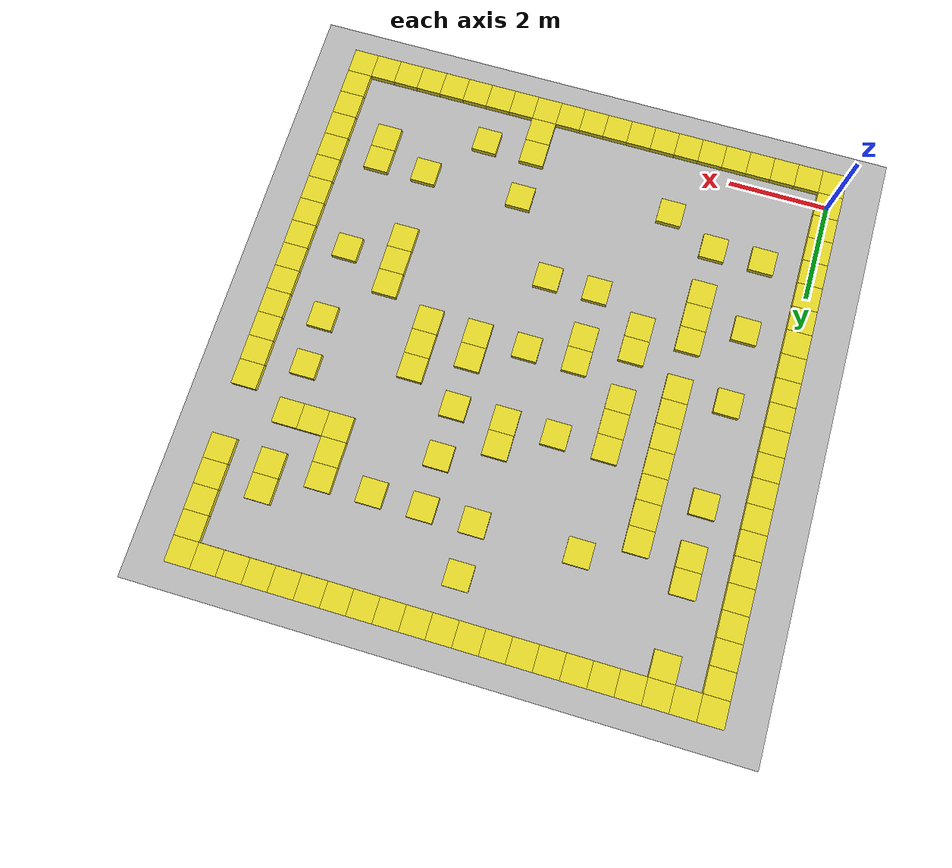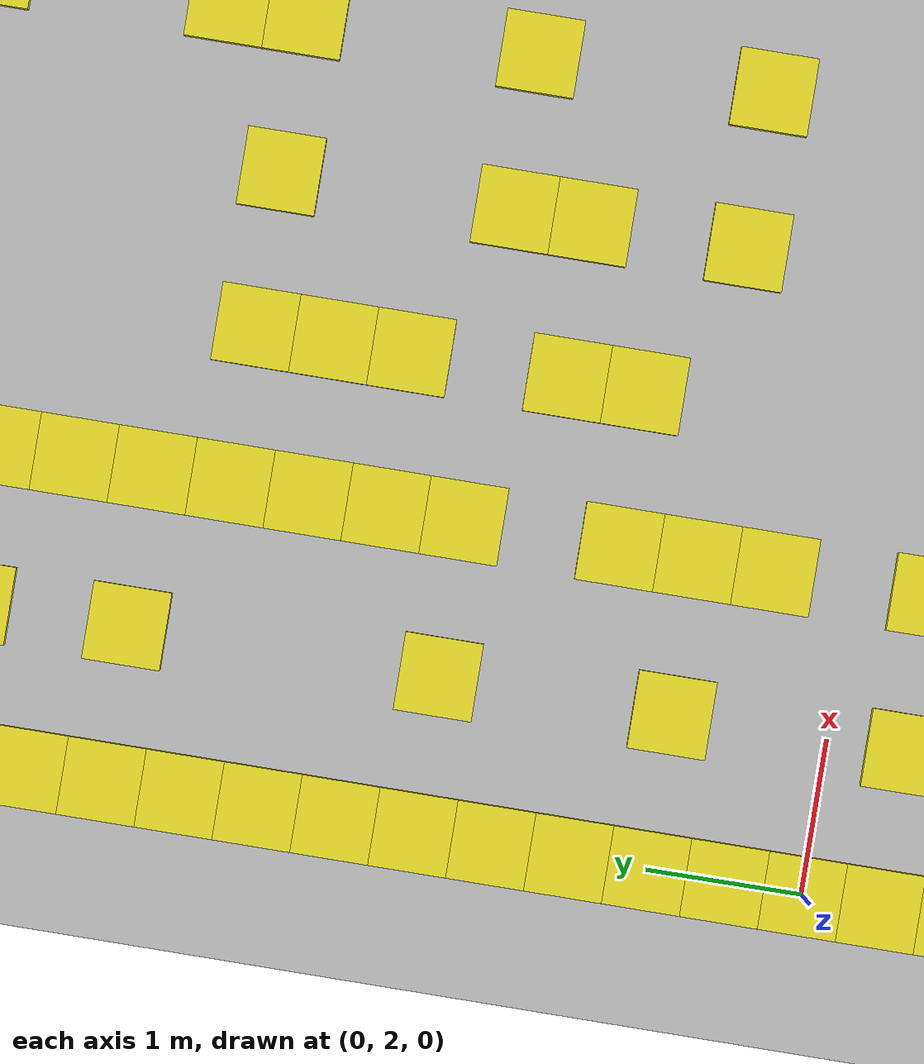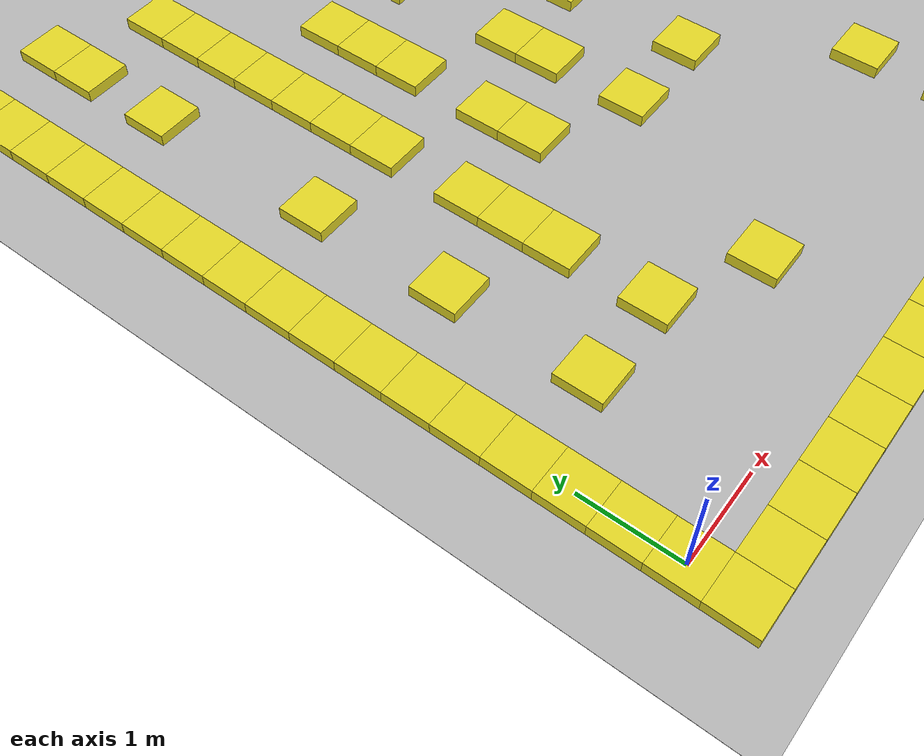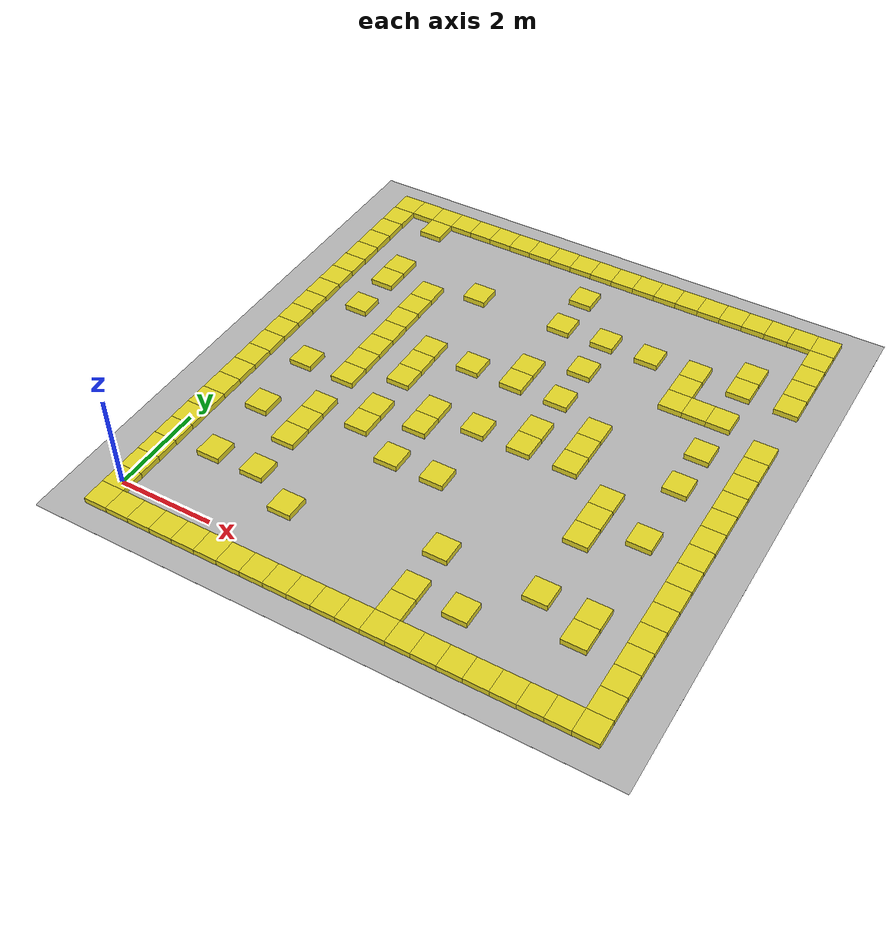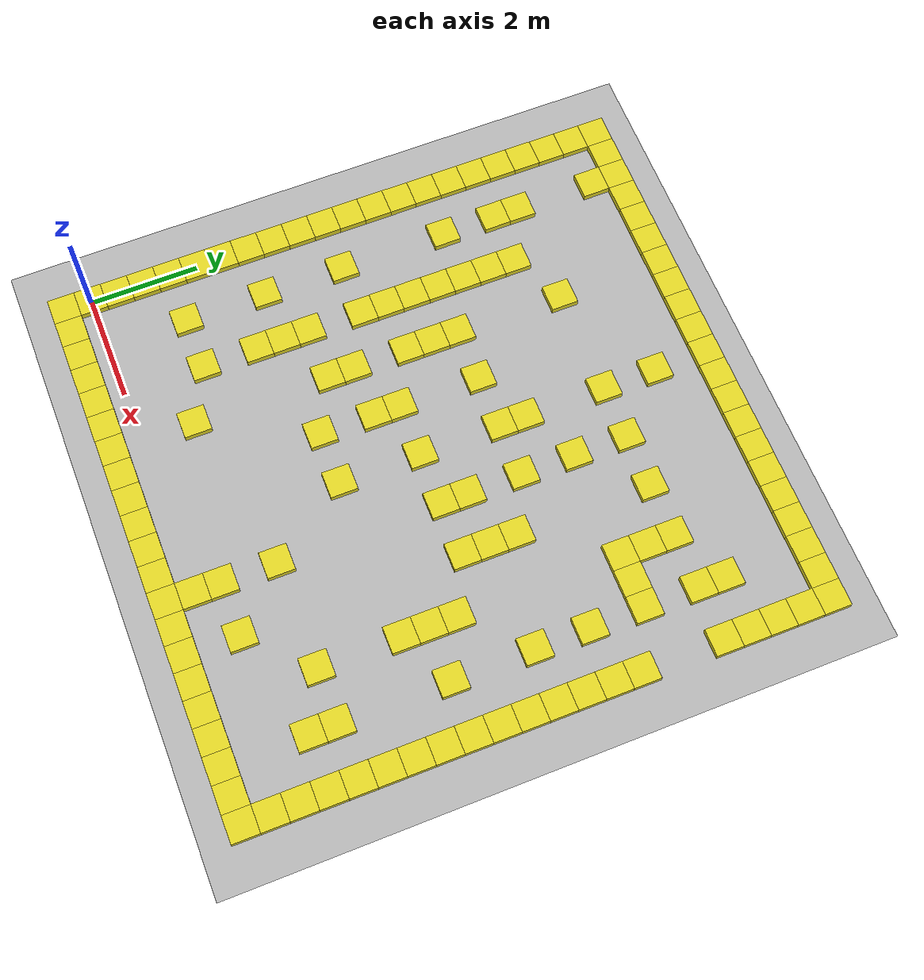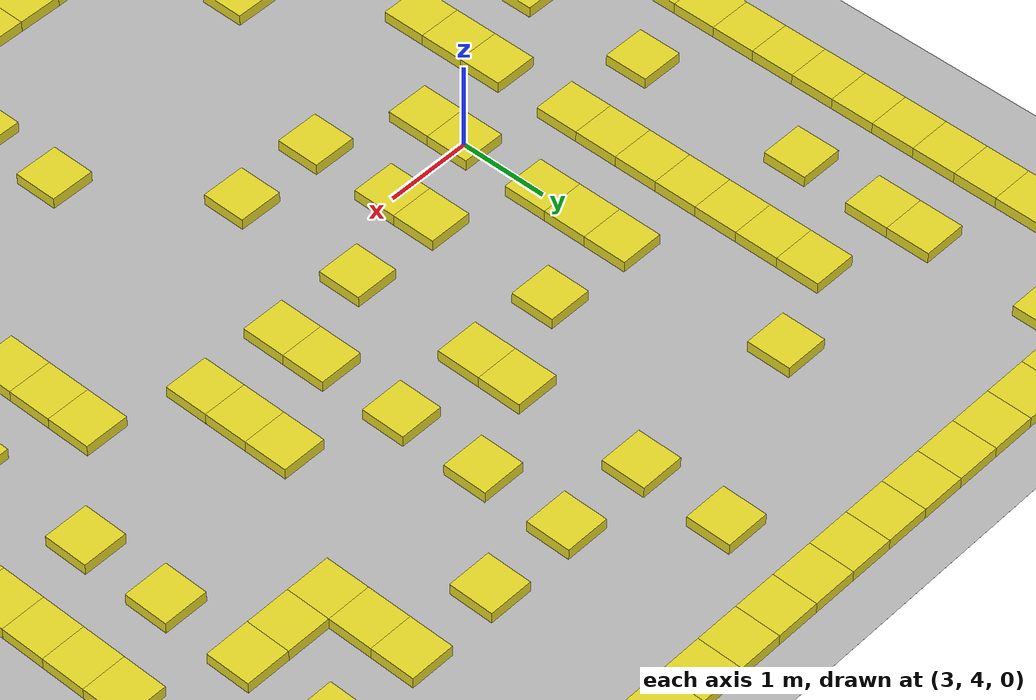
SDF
<sdf version="1.5">
 <world name="default">
  <include><uri>model://sun</uri></include>
  <include><uri>model://boundary</uri></include>
  <scene>
   <ambient>0.8 0.8 0.8 1</ambient>
   <background>0.8 0.9 1 1</background>
   <shadows>false</shadows>
   <grid>false</grid>
   <origin_visual>false</origin_visual>
  </scene>
  <physics name="default_physics" default="0" type="ode">
   <gravity>0 0 -9.8066</gravity>
   <ode>
    <solver>
     <type>quick</type>
     <iters>10</iters>
     <sor>1.3</sor>
     <use_dynamic_moi_rescaling>0</use_dynamic_moi_rescaling>
    </solver>
    <constraints>
     <cfm>0</cfm>
     <erp>0.2</erp>
     <contact_max_correcting_vel>100</contact_max_correcting_vel>
     <contact_surface_layer>0.001</contact_surface_layer>
    </constraints>
   </ode>
   <max_step_size>0.004</max_step_size>
   <real_time_factor>1</real_time_factor>
   <real_time_update_rate>250</real_time_update_rate>
   <magnetic_field>6.0e-6 2.3e-5 -4.2e-5</magnetic_field>
  </physics>
  <model name="unit_box_2">
   <pose>0.000000 -0.500000 0 0 -0 0</pose>
   <link name="link">
    <inertial>
     <mass>1</mass>
     <inertia><ixx>1</ixx><ixy>0</ixy><ixz>0</ixz><iyy>1</iyy><iyz>0</iyz><izz>1</izz></inertia>
    </inertial>
    <collision name="collision">
     <geometry><box><size>0.500000 0.500000 0.250000</size></box></geometry>
    </collision>
    <visual name="visual">
     <geometry><box><size>0.500000 0.500000 0.250000</size></box></geometry>
     <material>
      <script><uri>file://media/materials/scripts/gazebo.material</uri><name>Gazebo/Yellow</name></script>
     </material>
    </visual>
    <velocity_decay><linear>0</linear><angular>0</angular></velocity_decay>
   </link>
   <static>1</static>
  </model>
  <model name="unit_box_3">
   <pose>0.500000 -0.500000 0 0 -0 0</pose>
   <link name="link">
    <inertial>
     <mass>1</mass>
     <inertia><ixx>1</ixx><ixy>0</ixy><ixz>0</ixz><iyy>1</iyy><iyz>0</iyz><izz>1</izz></inertia>
    </inertial>
    <collision name="collision">
     <geometry><box><size>0.500000 0.500000 0.250000</size></box></geometry>
    </collision>
    <visual name="visual">
     <geometry><box><size>0.500000 0.500000 0.250000</size></box></geometry>
     <material>
      <script><uri>file://media/materials/scripts/gazebo.material</uri><name>Gazebo/Yellow</name></script>
     </material>
    </visual>
    <velocity_decay><linear>0</linear><angular>0</angular></velocity_decay>
   </link>
   <static>1</static>
  </model>
  <model name="unit_box_4">
   <pose>1.000000 -0.500000 0 0 -0 0</pose>
   <link name="link">
    <inertial>
     <mass>1</mass>
     <inertia><ixx>1</ixx><ixy>0</ixy><ixz>0</ixz><iyy>1</iyy><iyz>0</iyz><izz>1</izz></inertia>
    </inertial>
    <collision name="collision">
     <geometry><box><size>0.500000 0.500000 0.250000</size></box></geometry>
    </collision>
    <visual name="visual">
     <geometry><box><size>0.500000 0.500000 0.250000</size></box></geometry>
     <material>
      <script><uri>file://media/materials/scripts/gazebo.material</uri><name>Gazebo/Yellow</name></script>
     </material>
    </visual>
    <velocity_decay><linear>0</linear><angular>0</angular></velocity_decay>
   </link>
   <static>1</static>
  </model>
  <model name="unit_box_5">
   <pose>1.500000 -0.500000 0 0 -0 0</pose>
   <link name="link">
    <inertial>
     <mass>1</mass>
     <inertia><ixx>1</ixx><ixy>0</ixy><ixz>0</ixz><iyy>1</iyy><iyz>0</iyz><izz>1</izz></inertia>
    </inertial>
    <collision name="collision">
     <geometry><box><size>0.500000 0.500000 0.250000</size></box></geometry>
    </collision>
    <visual name="visual">
     <geometry><box><size>0.500000 0.500000 0.250000</size></box></geometry>
     <material>
      <script><uri>file://media/materials/scripts/gazebo.material</uri><name>Gazebo/Yellow</name></script>
     </material>
    </visual>
    <velocity_decay><linear>0</linear><angular>0</angular></velocity_decay>
   </link>
   <static>1</static>
  </model>
  <model name="unit_box_6">
   <pose>2.000000 -0.500000 0 0 -0 0</pose>
   <link name="link">
    <inertial>
     <mass>1</mass>
     <inertia><ixx>1</ixx><ixy>0</ixy><ixz>0</ixz><iyy>1</iyy><iyz>0</iyz><izz>1</izz></inertia>
    </inertial>
    <collision name="collision">
     <geometry><box><size>0.500000 0.500000 0.250000</size></box></geometry>
    </collision>
    <visual name="visual">
     <geometry><box><size>0.500000 0.500000 0.250000</size></box></geometry>
     <material>
      <script><uri>file://media/materials/scripts/gazebo.material</uri><name>Gazebo/Yellow</name></script>
     </material>
    </visual>
    <velocity_decay><linear>0</linear><angular>0</angular></velocity_decay>
   </link>
   <static>1</static>
  </model>
  <model name="unit_box_7">
   <pose>2.500000 -0.500000 0 0 -0 0</pose>
   <link name="link">
    <inertial>
     <mass>1</mass>
     <inertia><ixx>1</ixx><ixy>0</ixy><ixz>0</ixz><iyy>1</iyy><iyz>0</iyz><izz>1</izz></inertia>
    </inertial>
    <collision name="collision">
     <geometry><box><size>0.500000 0.500000 0.250000</size></box></geometry>
    </collision>
    <visual name="visual">
     <geometry><box><size>0.500000 0.500000 0.250000</size></box></geometry>
     <material>
      <script><uri>file://media/materials/scripts/gazebo.material</uri><name>Gazebo/Yellow</name></script>
     </material>
    </visual>
    <velocity_decay><linear>0</linear><angular>0</angular></velocity_decay>
   </link>
   <static>1</static>
  </model>
  <model name="unit_box_8">
   <pose>3.000000 -0.500000 0 0 -0 0</pose>
   <link name="link">
    <inertial>
     <mass>1</mass>
     <inertia><ixx>1</ixx><ixy>0</ixy><ixz>0</ixz><iyy>1</iyy><iyz>0</iyz><izz>1</izz></inertia>
    </inertial>
    <collision name="collision">
     <geometry><box><size>0.500000 0.500000 0.250000</size></box></geometry>
    </collision>
    <visual name="visual">
     <geometry><box><size>0.500000 0.500000 0.250000</size></box></geometry>
     <material>
      <script><uri>file://media/materials/scripts/gazebo.material</uri><name>Gazebo/Yellow</name></script>
     </material>
    </visual>
    <velocity_decay><linear>0</linear><angular>0</angular></velocity_decay>
   </link>
   <static>1</static>
  </model>
  <model name="unit_box_9">
   <pose>3.500000 -0.500000 0 0 -0 0</pose>
   <link name="link">
    <inertial>
     <mass>1</mass>
     <inertia><ixx>1</ixx><ixy>0</ixy><ixz>0</ixz><iyy>1</iyy><iyz>0</iyz><izz>1</izz></inertia>
    </inertial>
    <collision name="collision">
     <geometry><box><size>0.500000 0.500000 0.250000</size></box></geometry>
    </collision>
    <visual name="visual">
     <geometry><box><size>0.500000 0.500000 0.250000</size></box></geometry>
     <material>
      <script><uri>file://media/materials/scripts/gazebo.material</uri><name>Gazebo/Yellow</name></script>
     </material>
    </visual>
    <velocity_decay><linear>0</linear><angular>0</angular></velocity_decay>
   </link>
   <static>1</static>
  </model>
  <model name="unit_box_10">
   <pose>4.000000 -0.500000 0 0 -0 0</pose>
   <link name="link">
    <inertial>
     <mass>1</mass>
     <inertia><ixx>1</ixx><ixy>0</ixy><ixz>0</ixz><iyy>1</iyy><iyz>0</iyz><izz>1</izz></inertia>
    </inertial>
    <collision name="collision">
     <geometry><box><size>0.500000 0.500000 0.250000</size></box></geometry>
    </collision>
    <visual name="visual">
     <geometry><box><size>0.500000 0.500000 0.250000</size></box></geometry>
     <material>
      <script><uri>file://media/materials/scripts/gazebo.material</uri><name>Gazebo/Yellow</name></script>
     </material>
    </visual>
    <velocity_decay><linear>0</linear><angular>0</angular></velocity_decay>
   </link>
   <static>1</static>
  </model>
  <model name="unit_box_11">
   <pose>4.500000 -0.500000 0 0 -0 0</pose>
   <link name="link">
    <inertial>
     <mass>1</mass>
     <inertia><ixx>1</ixx><ixy>0</ixy><ixz>0</ixz><iyy>1</iyy><iyz>0</iyz><izz>1</izz></inertia>
    </inertial>
    <collision name="collision">
     <geometry><box><size>0.500000 0.500000 0.250000</size></box></geometry>
    </collision>
    <visual name="visual">
     <geometry><box><size>0.500000 0.500000 0.250000</size></box></geometry>
     <material>
      <script><uri>file://media/materials/scripts/gazebo.material</uri><name>Gazebo/Yellow</name></script>
     </material>
    </visual>
    <velocity_decay><linear>0</linear><angular>0</angular></velocity_decay>
   </link>
   <static>1</static>
  </model>
  <model name="unit_box_12">
   <pose>5.000000 -0.500000 0 0 -0 0</pose>
   <link name="link">
    <inertial>
     <mass>1</mass>
     <inertia><ixx>1</ixx><ixy>0</ixy><ixz>0</ixz><iyy>1</iyy><iyz>0</iyz><izz>1</izz></inertia>
    </inertial>
    <collision name="collision">
     <geometry><box><size>0.500000 0.500000 0.250000</size></box></geometry>
    </collision>
    <visual name="visual">
     <geometry><box><size>0.500000 0.500000 0.250000</size></box></geometry>
     <material>
      <script><uri>file://media/materials/scripts/gazebo.material</uri><name>Gazebo/Yellow</name></script>
     </material>
    </visual>
    <velocity_decay><linear>0</linear><angular>0</angular></velocity_decay>
   </link>
   <static>1</static>
  </model>
  <model name="unit_box_13">
   <pose>5.500000 -0.500000 0 0 -0 0</pose>
   <link name="link">
    <inertial>
     <mass>1</mass>
     <inertia><ixx>1</ixx><ixy>0</ixy><ixz>0</ixz><iyy>1</iyy><iyz>0</iyz><izz>1</izz></inertia>
    </inertial>
    <collision name="collision">
     <geometry><box><size>0.500000 0.500000 0.250000</size></box></geometry>
    </collision>
    <visual name="visual">
     <geometry><box><size>0.500000 0.500000 0.250000</size></box></geometry>
     <material>
      <script><uri>file://media/materials/scripts/gazebo.material</uri><name>Gazebo/Yellow</name></script>
     </material>
    </visual>
    <velocity_decay><linear>0</linear><angular>0</angular></velocity_decay>
   </link>
   <static>1</static>
  </model>
  <model name="unit_box_14">
   <pose>6.000000 -0.500000 0 0 -0 0</pose>
   <link name="link">
    <inertial>
     <mass>1</mass>
     <inertia><ixx>1</ixx><ixy>0</ixy><ixz>0</ixz><iyy>1</iyy><iyz>0</iyz><izz>1</izz></inertia>
    </inertial>
    <collision name="collision">
     <geometry><box><size>0.500000 0.500000 0.250000</size></box></geometry>
    </collision>
    <visual name="visual">
     <geometry><box><size>0.500000 0.500000 0.250000</size></box></geometry>
     <material>
      <script><uri>file://media/materials/scripts/gazebo.material</uri><name>Gazebo/Yellow</name></script>
     </material>
    </visual>
    <velocity_decay><linear>0</linear><angular>0</angular></velocity_decay>
   </link>
   <static>1</static>
  </model>
  <model name="unit_box_15">
   <pose>6.500000 -0.500000 0 0 -0 0</pose>
   <link name="link">
    <inertial>
     <mass>1</mass>
     <inertia><ixx>1</ixx><ixy>0</ixy><ixz>0</ixz><iyy>1</iyy><iyz>0</iyz><izz>1</izz></inertia>
    </inertial>
    <collision name="collision">
     <geometry><box><size>0.500000 0.500000 0.250000</size></box></geometry>
    </collision>
    <visual name="visual">
     <geometry><box><size>0.500000 0.500000 0.250000</size></box></geometry>
     <material>
      <script><uri>file://media/materials/scripts/gazebo.material</uri><name>Gazebo/Yellow</name></script>
     </material>
    </visual>
    <velocity_decay><linear>0</linear><angular>0</angular></velocity_decay>
   </link>
   <static>1</static>
  </model>
  <model name="unit_box_16">
   <pose>7.000000 -0.500000 0 0 -0 0</pose>
   <link name="link">
    <inertial>
     <mass>1</mass>
     <inertia><ixx>1</ixx><ixy>0</ixy><ixz>0</ixz><iyy>1</iyy><iyz>0</iyz><izz>1</izz></inertia>
    </inertial>
    <collision name="collision">
     <geometry><box><size>0.500000 0.500000 0.250000</size></box></geometry>
    </collision>
    <visual name="visual">
     <geometry><box><size>0.500000 0.500000 0.250000</size></box></geometry>
     <material>
      <script><uri>file://media/materials/scripts/gazebo.material</uri><name>Gazebo/Yellow</name></script>
     </material>
    </visual>
    <velocity_decay><linear>0</linear><angular>0</angular></velocity_decay>
   </link>
   <static>1</static>
  </model>
  <model name="unit_box_17">
   <pose>7.500000 -0.500000 0 0 -0 0</pose>
   <link name="link">
    <inertial>
     <mass>1</mass>
     <inertia><ixx>1</ixx><ixy>0</ixy><ixz>0</ixz><iyy>1</iyy><iyz>0</iyz><izz>1</izz></inertia>
    </inertial>
    <collision name="collision">
     <geometry><box><size>0.500000 0.500000 0.250000</size></box></geometry>
    </collision>
    <visual name="visual">
     <geometry><box><size>0.500000 0.500000 0.250000</size></box></geometry>
     <material>
      <script><uri>file://media/materials/scripts/gazebo.material</uri><name>Gazebo/Yellow</name></script>
     </material>
    </visual>
    <velocity_decay><linear>0</linear><angular>0</angular></velocity_decay>
   </link>
   <static>1</static>
  </model>
  <model name="unit_box_18">
   <pose>8.000000 -0.500000 0 0 -0 0</pose>
   <link name="link">
    <inertial>
     <mass>1</mass>
     <inertia><ixx>1</ixx><ixy>0</ixy><ixz>0</ixz><iyy>1</iyy><iyz>0</iyz><izz>1</izz></inertia>
    </inertial>
    <collision name="collision">
     <geometry><box><size>0.500000 0.500000 0.250000</size></box></geometry>
    </collision>
    <visual name="visual">
     <geometry><box><size>0.500000 0.500000 0.250000</size></box></geometry>
     <material>
      <script><uri>file://media/materials/scripts/gazebo.material</uri><name>Gazebo/Yellow</name></script>
     </material>
    </visual>
    <velocity_decay><linear>0</linear><angular>0</angular></velocity_decay>
   </link>
   <static>1</static>
  </model>
  <model name="unit_box_19">
   <pose>8.500000 -0.500000 0 0 -0 0</pose>
   <link name="link">
    <inertial>
     <mass>1</mass>
     <inertia><ixx>1</ixx><ixy>0</ixy><ixz>0</ixz><iyy>1</iyy><iyz>0</iyz><izz>1</izz></inertia>
    </inertial>
    <collision name="collision">
     <geometry><box><size>0.500000 0.500000 0.250000</size></box></geometry>
    </collision>
    <visual name="visual">
     <geometry><box><size>0.500000 0.500000 0.250000</size></box></geometry>
     <material>
      <script><uri>file://media/materials/scripts/gazebo.material</uri><name>Gazebo/Yellow</name></script>
     </material>
    </visual>
    <velocity_decay><linear>0</linear><angular>0</angular></velocity_decay>
   </link>
   <static>1</static>
  </model>
  <model name="unit_box_20">
   <pose>9.000000 -0.500000 0 0 -0 0</pose>
   <link name="link">
    <inertial>
     <mass>1</mass>
     <inertia><ixx>1</ixx><ixy>0</ixy><ixz>0</ixz><iyy>1</iyy><iyz>0</iyz><izz>1</izz></inertia>
    </inertial>
    <collision name="collision">
     <geometry><box><size>0.500000 0.500000 0.250000</size></box></geometry>
    </collision>
    <visual name="visual">
     <geometry><box><size>0.500000 0.500000 0.250000</size></box></geometry>
     <material>
      <script><uri>file://media/materials/scripts/gazebo.material</uri><name>Gazebo/Yellow</name></script>
     </material>
    </visual>
    <velocity_decay><linear>0</linear><angular>0</angular></velocity_decay>
   </link>
   <static>1</static>
  </model>
  <model name="unit_box_21">
   <pose>9.500000 -0.500000 0 0 -0 0</pose>
   <link name="link">
    <inertial>
     <mass>1</mass>
     <inertia><ixx>1</ixx><ixy>0</ixy><ixz>0</ixz><iyy>1</iyy><iyz>0</iyz><izz>1</izz></inertia>
    </inertial>
    <collision name="collision">
     <geometry><box><size>0.500000 0.500000 0.250000</size></box></geometry>
    </collision>
    <visual name="visual">
     <geometry><box><size>0.500000 0.500000 0.250000</size></box></geometry>
     <material>
      <script><uri>file://media/materials/scripts/gazebo.material</uri><name>Gazebo/Yellow</name></script>
     </material>
    </visual>
    <velocity_decay><linear>0</linear><angular>0</angular></velocity_decay>
   </link>
   <static>1</static>
  </model>
  <model name="unit_box_22">
   <pose>10.000000 -0.500000 0 0 -0 0</pose>
   <link name="link">
    <inertial>
     <mass>1</mass>
     <inertia><ixx>1</ixx><ixy>0</ixy><ixz>0</ixz><iyy>1</iyy><iyz>0</iyz><izz>1</izz></inertia>
    </inertial>
    <collision name="collision">
     <geometry><box><size>0.500000 0.500000 0.250000</size></box></geometry>
    </collision>
    <visual name="visual">
     <geometry><box><size>0.500000 0.500000 0.250000</size></box></geometry>
     <material>
      <script><uri>file://media/materials/scripts/gazebo.material</uri><name>Gazebo/Yellow</name></script>
     </material>
    </visual>
    <velocity_decay><linear>0</linear><angular>0</angular></velocity_decay>
   </link>
   <static>1</static>
  </model>
  <model name="unit_box_23">
   <link name="link">
    <inertial>
     <mass>1</mass>
     <inertia><ixx>1</ixx><ixy>0</ixy><ixz>0</ixz><iyy>1</iyy><iyz>0</iyz><izz>1</izz></inertia>
    </inertial>
    <collision name="collision">
     <geometry><box><size>0.500000 0.500000 0.250000</size></box></geometry>
    </collision>
    <visual name="visual">
     <geometry><box><size>0.500000 0.500000 0.250000</size></box></geometry>
     <material>
      <script><uri>file://media/materials/scripts/gazebo.material</uri><name>Gazebo/Yellow</name></script>
     </material>
    </visual>
    <velocity_decay><linear>0</linear><angular>0</angular></velocity_decay>
   </link>
   <static>1</static>
  </model>
  <model name="unit_box_24">
   <pose>0.000000 0.500000 0 0 -0 0</pose>
   <link name="link">
    <inertial>
     <mass>1</mass>
     <inertia><ixx>1</ixx><ixy>0</ixy><ixz>0</ixz><iyy>1</iyy><iyz>0</iyz><izz>1</izz></inertia>
    </inertial>
    <collision name="collision">
     <geometry><box><size>0.500000 0.500000 0.250000</size></box></geometry>
    </collision>
    <visual name="visual">
     <geometry><box><size>0.500000 0.500000 0.250000</size></box></geometry>
     <material>
      <script><uri>file://media/materials/scripts/gazebo.material</uri><name>Gazebo/Yellow</name></script>
     </material>
    </visual>
    <velocity_decay><linear>0</linear><angular>0</angular></velocity_decay>
   </link>
   <static>1</static>
  </model>
  <model name="unit_box_25">
   <pose>0.000000 1.000000 0 0 -0 0</pose>
   <link name="link">
    <inertial>
     <mass>1</mass>
     <inertia><ixx>1</ixx><ixy>0</ixy><ixz>0</ixz><iyy>1</iyy><iyz>0</iyz><izz>1</izz></inertia>
    </inertial>
    <collision name="collision">
     <geometry><box><size>0.500000 0.500000 0.250000</size></box></geometry>
    </collision>
    <visual name="visual">
     <geometry><box><size>0.500000 0.500000 0.250000</size></box></geometry>
     <material>
      <script><uri>file://media/materials/scripts/gazebo.material</uri><name>Gazebo/Yellow</name></script>
     </material>
    </visual>
    <velocity_decay><linear>0</linear><angular>0</angular></velocity_decay>
   </link>
   <static>1</static>
  </model>
  <model name="unit_box_26">
   <pose>0.000000 1.500000 0 0 -0 0</pose>
   <link name="link">
    <inertial>
     <mass>1</mass>
     <inertia><ixx>1</ixx><ixy>0</ixy><ixz>0</ixz><iyy>1</iyy><iyz>0</iyz><izz>1</izz></inertia>
    </inertial>
    <collision name="collision">
     <geometry><box><size>0.500000 0.500000 0.250000</size></box></geometry>
    </collision>
    <visual name="visual">
     <geometry><box><size>0.500000 0.500000 0.250000</size></box></geometry>
     <material>
      <script><uri>file://media/materials/scripts/gazebo.material</uri><name>Gazebo/Yellow</name></script>
     </material>
    </visual>
    <velocity_decay><linear>0</linear><angular>0</angular></velocity_decay>
   </link>
   <static>1</static>
  </model>
  <model name="unit_box_27">
   <pose>0.000000 2.000000 0 0 -0 0</pose>
   <link name="link">
    <inertial>
     <mass>1</mass>
     <inertia><ixx>1</ixx><ixy>0</ixy><ixz>0</ixz><iyy>1</iyy><iyz>0</iyz><izz>1</izz></inertia>
    </inertial>
    <collision name="collision">
     <geometry><box><size>0.500000 0.500000 0.250000</size></box></geometry>
    </collision>
    <visual name="visual">
     <geometry><box><size>0.500000 0.500000 0.250000</size></box></geometry>
     <material>
      <script><uri>file://media/materials/scripts/gazebo.material</uri><name>Gazebo/Yellow</name></script>
     </material>
    </visual>
    <velocity_decay><linear>0</linear><angular>0</angular></velocity_decay>
   </link>
   <static>1</static>
  </model>
  <model name="unit_box_28">
   <pose>0.000000 2.500000 0 0 -0 0</pose>
   <link name="link">
    <inertial>
     <mass>1</mass>
     <inertia><ixx>1</ixx><ixy>0</ixy><ixz>0</ixz><iyy>1</iyy><iyz>0</iyz><izz>1</izz></inertia>
    </inertial>
    <collision name="collision">
     <geometry><box><size>0.500000 0.500000 0.250000</size></box></geometry>
    </collision>
    <visual name="visual">
     <geometry><box><size>0.500000 0.500000 0.250000</size></box></geometry>
     <material>
      <script><uri>file://media/materials/scripts/gazebo.material</uri><name>Gazebo/Yellow</name></script>
     </material>
    </visual>
    <velocity_decay><linear>0</linear><angular>0</angular></velocity_decay>
   </link>
   <static>1</static>
  </model>
  <model name="unit_box_29">
   <pose>0.000000 3.000000 0 0 -0 0</pose>
   <link name="link">
    <inertial>
     <mass>1</mass>
     <inertia><ixx>1</ixx><ixy>0</ixy><ixz>0</ixz><iyy>1</iyy><iyz>0</iyz><izz>1</izz></inertia>
    </inertial>
    <collision name="collision">
     <geometry><box><size>0.500000 0.500000 0.250000</size></box></geometry>
    </collision>
    <visual name="visual">
     <geometry><box><size>0.500000 0.500000 0.250000</size></box></geometry>
     <material>
      <script><uri>file://media/materials/scripts/gazebo.material</uri><name>Gazebo/Yellow</name></script>
     </material>
    </visual>
    <velocity_decay><linear>0</linear><angular>0</angular></velocity_decay>
   </link>
   <static>1</static>
  </model>
  <model name="unit_box_30">
   <pose>0.000000 3.500000 0 0 -0 0</pose>
   <link name="link">
    <inertial>
     <mass>1</mass>
     <inertia><ixx>1</ixx><ixy>0</ixy><ixz>0</ixz><iyy>1</iyy><iyz>0</iyz><izz>1</izz></inertia>
    </inertial>
    <collision name="collision">
     <geometry><box><size>0.500000 0.500000 0.250000</size></box></geometry>
    </collision>
    <visual name="visual">
     <geometry><box><size>0.500000 0.500000 0.250000</size></box></geometry>
     <material>
      <script><uri>file://media/materials/scripts/gazebo.material</uri><name>Gazebo/Yellow</name></script>
     </material>
    </visual>
    <velocity_decay><linear>0</linear><angular>0</angular></velocity_decay>
   </link>
   <static>1</static>
  </model>
  <model name="unit_box_31">
   <pose>0.000000 4.000000 0 0 -0 0</pose>
   <link name="link">
    <inertial>
     <mass>1</mass>
     <inertia><ixx>1</ixx><ixy>0</ixy><ixz>0</ixz><iyy>1</iyy><iyz>0</iyz><izz>1</izz></inertia>
    </inertial>
    <collision name="collision">
     <geometry><box><size>0.500000 0.500000 0.250000</size></box></geometry>
    </collision>
    <visual name="visual">
     <geometry><box><size>0.500000 0.500000 0.250000</size></box></geometry>
     <material>
      <script><uri>file://media/materials/scripts/gazebo.material</uri><name>Gazebo/Yellow</name></script>
     </material>
    </visual>
    <velocity_decay><linear>0</linear><angular>0</angular></velocity_decay>
   </link>
   <static>1</static>
  </model>
  <model name="unit_box_32">
   <pose>0.000000 4.500000 0 0 -0 0</pose>
   <link name="link">
    <inertial>
     <mass>1</mass>
     <inertia><ixx>1</ixx><ixy>0</ixy><ixz>0</ixz><iyy>1</iyy><iyz>0</iyz><izz>1</izz></inertia>
    </inertial>
    <collision name="collision">
     <geometry><box><size>0.500000 0.500000 0.250000</size></box></geometry>
    </collision>
    <visual name="visual">
     <geometry><box><size>0.500000 0.500000 0.250000</size></box></geometry>
     <material>
      <script><uri>file://media/materials/scripts/gazebo.material</uri><name>Gazebo/Yellow</name></script>
     </material>
    </visual>
    <velocity_decay><linear>0</linear><angular>0</angular></velocity_decay>
   </link>
   <static>1</static>
  </model>
  <model name="unit_box_33">
   <pose>0.000000 5.000000 0 0 -0 0</pose>
   <link name="link">
    <inertial>
     <mass>1</mass>
     <inertia><ixx>1</ixx><ixy>0</ixy><ixz>0</ixz><iyy>1</iyy><iyz>0</iyz><izz>1</izz></inertia>
    </inertial>
    <collision name="collision">
     <geometry><box><size>0.500000 0.500000 0.250000</size></box></geometry>
    </collision>
    <visual name="visual">
     <geometry><box><size>0.500000 0.500000 0.250000</size></box></geometry>
     <material>
      <script><uri>file://media/materials/scripts/gazebo.material</uri><name>Gazebo/Yellow</name></script>
     </material>
    </visual>
    <velocity_decay><linear>0</linear><angular>0</angular></velocity_decay>
   </link>
   <static>1</static>
  </model>
  <model name="unit_box_34">
   <pose>0.000000 5.500000 0 0 -0 0</pose>
   <link name="link">
    <inertial>
     <mass>1</mass>
     <inertia><ixx>1</ixx><ixy>0</ixy><ixz>0</ixz><iyy>1</iyy><iyz>0</iyz><izz>1</izz></inertia>
    </inertial>
    <collision name="collision">
     <geometry><box><size>0.500000 0.500000 0.250000</size></box></geometry>
    </collision>
    <visual name="visual">
     <geometry><box><size>0.500000 0.500000 0.250000</size></box></geometry>
     <material>
      <script><uri>file://media/materials/scripts/gazebo.material</uri><name>Gazebo/Yellow</name></script>
     </material>
    </visual>
    <velocity_decay><linear>0</linear><angular>0</angular></velocity_decay>
   </link>
   <static>1</static>
  </model>
  <model name="unit_box_35">
   <pose>0.000000 6.000000 0 0 -0 0</pose>
   <link name="link">
    <inertial>
     <mass>1</mass>
     <inertia><ixx>1</ixx><ixy>0</ixy><ixz>0</ixz><iyy>1</iyy><iyz>0</iyz><izz>1</izz></inertia>
    </inertial>
    <collision name="collision">
     <geometry><box><size>0.500000 0.500000 0.250000</size></box></geometry>
    </collision>
    <visual name="visual">
     <geometry><box><size>0.500000 0.500000 0.250000</size></box></geometry>
     <material>
      <script><uri>file://media/materials/scripts/gazebo.material</uri><name>Gazebo/Yellow</name></script>
     </material>
    </visual>
    <velocity_decay><linear>0</linear><angular>0</angular></velocity_decay>
   </link>
   <static>1</static>
  </model>
  <model name="unit_box_36">
   <pose>0.000000 6.500000 0 0 -0 0</pose>
   <link name="link">
    <inertial>
     <mass>1</mass>
     <inertia><ixx>1</ixx><ixy>0</ixy><ixz>0</ixz><iyy>1</iyy><iyz>0</iyz><izz>1</izz></inertia>
    </inertial>
    <collision name="collision">
     <geometry><box><size>0.500000 0.500000 0.250000</size></box></geometry>
    </collision>
    <visual name="visual">
     <geometry><box><size>0.500000 0.500000 0.250000</size></box></geometry>
     <material>
      <script><uri>file://media/materials/scripts/gazebo.material</uri><name>Gazebo/Yellow</name></script>
     </material>
    </visual>
    <velocity_decay><linear>0</linear><angular>0</angular></velocity_decay>
   </link>
   <static>1</static>
  </model>
  <model name="unit_box_37">
   <pose>0.000000 7.000000 0 0 -0 0</pose>
   <link name="link">
    <inertial>
     <mass>1</mass>
     <inertia><ixx>1</ixx><ixy>0</ixy><ixz>0</ixz><iyy>1</iyy><iyz>0</iyz><izz>1</izz></inertia>
    </inertial>
    <collision name="collision">
     <geometry><box><size>0.500000 0.500000 0.250000</size></box></geometry>
    </collision>
    <visual name="visual">
     <geometry><box><size>0.500000 0.500000 0.250000</size></box></geometry>
     <material>
      <script><uri>file://media/materials/scripts/gazebo.material</uri><name>Gazebo/Yellow</name></script>
     </material>
    </visual>
    <velocity_decay><linear>0</linear><angular>0</angular></velocity_decay>
   </link>
   <static>1</static>
  </model>
  <model name="unit_box_38">
   <pose>0.000000 7.500000 0 0 -0 0</pose>
   <link name="link">
    <inertial>
     <mass>1</mass>
     <inertia><ixx>1</ixx><ixy>0</ixy><ixz>0</ixz><iyy>1</iyy><iyz>0</iyz><izz>1</izz></inertia>
    </inertial>
    <collision name="collision">
     <geometry><box><size>0.500000 0.500000 0.250000</size></box></geometry>
    </collision>
    <visual name="visual">
     <geometry><box><size>0.500000 0.500000 0.250000</size></box></geometry>
     <material>
      <script><uri>file://media/materials/scripts/gazebo.material</uri><name>Gazebo/Yellow</name></script>
     </material>
    </visual>
    <velocity_decay><linear>0</linear><angular>0</angular></velocity_decay>
   </link>
   <static>1</static>
  </model>
  <model name="unit_box_39">
   <pose>0.000000 8.000000 0 0 -0 0</pose>
   <link name="link">
    <inertial>
     <mass>1</mass>
     <inertia><ixx>1</ixx><ixy>0</ixy><ixz>0</ixz><iyy>1</iyy><iyz>0</iyz><izz>1</izz></inertia>
    </inertial>
    <collision name="collision">
     <geometry><box><size>0.500000 0.500000 0.250000</size></box></geometry>
    </collision>
    <visual name="visual">
     <geometry><box><size>0.500000 0.500000 0.250000</size></box></geometry>
     <material>
      <script><uri>file://media/materials/scripts/gazebo.material</uri><name>Gazebo/Yellow</name></script>
     </material>
    </visual>
    <velocity_decay><linear>0</linear><angular>0</angular></velocity_decay>
   </link>
   <static>1</static>
  </model>
  <model name="unit_box_40">
   <pose>0.000000 8.500000 0 0 -0 0</pose>
   <link name="link">
    <inertial>
     <mass>1</mass>
     <inertia><ixx>1</ixx><ixy>0</ixy><ixz>0</ixz><iyy>1</iyy><iyz>0</iyz><izz>1</izz></inertia>
    </inertial>
    <collision name="collision">
     <geometry><box><size>0.500000 0.500000 0.250000</size></box></geometry>
    </collision>
    <visual name="visual">
     <geometry><box><size>0.500000 0.500000 0.250000</size></box></geometry>
     <material>
      <script><uri>file://media/materials/scripts/gazebo.material</uri><name>Gazebo/Yellow</name></script>
     </material>
    </visual>
    <velocity_decay><linear>0</linear><angular>0</angular></velocity_decay>
   </link>
   <static>1</static>
  </model>
  <model name="unit_box_41">
   <pose>0.000000 9.000000 0 0 -0 0</pose>
   <link name="link">
    <inertial>
     <mass>1</mass>
     <inertia><ixx>1</ixx><ixy>0</ixy><ixz>0</ixz><iyy>1</iyy><iyz>0</iyz><izz>1</izz></inertia>
    </inertial>
    <collision name="collision">
     <geometry><box><size>0.500000 0.500000 0.250000</size></box></geometry>
    </collision>
    <visual name="visual">
     <geometry><box><size>0.500000 0.500000 0.250000</size></box></geometry>
     <material>
      <script><uri>file://media/materials/scripts/gazebo.material</uri><name>Gazebo/Yellow</name></script>
     </material>
    </visual>
    <velocity_decay><linear>0</linear><angular>0</angular></velocity_decay>
   </link>
   <static>1</static>
  </model>
  <model name="unit_box_42">
   <pose>0.000000 9.500000 0 0 -0 0</pose>
   <link name="link">
    <inertial>
     <mass>1</mass>
     <inertia><ixx>1</ixx><ixy>0</ixy><ixz>0</ixz><iyy>1</iyy><iyz>0</iyz><izz>1</izz></inertia>
    </inertial>
    <collision name="collision">
     <geometry><box><size>0.500000 0.500000 0.250000</size></box></geometry>
    </collision>
    <visual name="visual">
     <geometry><box><size>0.500000 0.500000 0.250000</size></box></geometry>
     <material>
      <script><uri>file://media/materials/scripts/gazebo.material</uri><name>Gazebo/Yellow</name></script>
     </material>
    </visual>
    <velocity_decay><linear>0</linear><angular>0</angular></velocity_decay>
   </link>
   <static>1</static>
  </model>
  <model name="unit_box_43">
   <pose>0.000000 10.000000 0 0 -0 0</pose>
   <link name="link">
    <inertial>
     <mass>1</mass>
     <inertia><ixx>1</ixx><ixy>0</ixy><ixz>0</ixz><iyy>1</iyy><iyz>0</iyz><izz>1</izz></inertia>
    </inertial>
    <collision name="collision">
     <geometry><box><size>0.500000 0.500000 0.250000</size></box></geometry>
    </collision>
    <visual name="visual">
     <geometry><box><size>0.500000 0.500000 0.250000</size></box></geometry>
     <material>
      <script><uri>file://media/materials/scripts/gazebo.material</uri><name>Gazebo/Yellow</name></script>
     </material>
    </visual>
    <velocity_decay><linear>0</linear><angular>0</angular></velocity_decay>
   </link>
   <static>1</static>
  </model>
  <model name="unit_box_44">
   <pose>0.500000 10.000000 0 0 -0 0</pose>
   <link name="link">
    <inertial>
     <mass>1</mass>
     <inertia><ixx>1</ixx><ixy>0</ixy><ixz>0</ixz><iyy>1</iyy><iyz>0</iyz><izz>1</izz></inertia>
    </inertial>
    <collision name="collision">
     <geometry><box><size>0.500000 0.500000 0.250000</size></box></geometry>
    </collision>
    <visual name="visual">
     <geometry><box><size>0.500000 0.500000 0.250000</size></box></geometry>
     <material>
      <script><uri>file://media/materials/scripts/gazebo.material</uri><name>Gazebo/Yellow</name></script>
     </material>
    </visual>
    <velocity_decay><linear>0</linear><angular>0</angular></velocity_decay>
   </link>
   <static>1</static>
  </model>
  <model name="unit_box_45">
   <pose>1.000000 10.000000 0 0 -0 0</pose>
   <link name="link">
    <inertial>
     <mass>1</mass>
     <inertia><ixx>1</ixx><ixy>0</ixy><ixz>0</ixz><iyy>1</iyy><iyz>0</iyz><izz>1</izz></inertia>
    </inertial>
    <collision name="collision">
     <geometry><box><size>0.500000 0.500000 0.250000</size></box></geometry>
    </collision>
    <visual name="visual">
     <geometry><box><size>0.500000 0.500000 0.250000</size></box></geometry>
     <material>
      <script><uri>file://media/materials/scripts/gazebo.material</uri><name>Gazebo/Yellow</name></script>
     </material>
    </visual>
    <velocity_decay><linear>0</linear><angular>0</angular></velocity_decay>
   </link>
   <static>1</static>
  </model>
  <model name="unit_box_46">
   <pose>1.500000 10.000000 0 0 -0 0</pose>
   <link name="link">
    <inertial>
     <mass>1</mass>
     <inertia><ixx>1</ixx><ixy>0</ixy><ixz>0</ixz><iyy>1</iyy><iyz>0</iyz><izz>1</izz></inertia>
    </inertial>
    <collision name="collision">
     <geometry><box><size>0.500000 0.500000 0.250000</size></box></geometry>
    </collision>
    <visual name="visual">
     <geometry><box><size>0.500000 0.500000 0.250000</size></box></geometry>
     <material>
      <script><uri>file://media/materials/scripts/gazebo.material</uri><name>Gazebo/Yellow</name></script>
     </material>
    </visual>
    <velocity_decay><linear>0</linear><angular>0</angular></velocity_decay>
   </link>
   <static>1</static>
  </model>
  <model name="unit_box_47">
   <pose>2.000000 10.000000 0 0 -0 0</pose>
   <link name="link">
    <inertial>
     <mass>1</mass>
     <inertia><ixx>1</ixx><ixy>0</ixy><ixz>0</ixz><iyy>1</iyy><iyz>0</iyz><izz>1</izz></inertia>
    </inertial>
    <collision name="collision">
     <geometry><box><size>0.500000 0.500000 0.250000</size></box></geometry>
    </collision>
    <visual name="visual">
     <geometry><box><size>0.500000 0.500000 0.250000</size></box></geometry>
     <material>
      <script><uri>file://media/materials/scripts/gazebo.material</uri><name>Gazebo/Yellow</name></script>
     </material>
    </visual>
    <velocity_decay><linear>0</linear><angular>0</angular></velocity_decay>
   </link>
   <static>1</static>
  </model>
  <model name="unit_box_48">
   <pose>2.500000 10.000000 0 0 -0 0</pose>
   <link name="link">
    <inertial>
     <mass>1</mass>
     <inertia><ixx>1</ixx><ixy>0</ixy><ixz>0</ixz><iyy>1</iyy><iyz>0</iyz><izz>1</izz></inertia>
    </inertial>
    <collision name="collision">
     <geometry><box><size>0.500000 0.500000 0.250000</size></box></geometry>
    </collision>
    <visual name="visual">
     <geometry><box><size>0.500000 0.500000 0.250000</size></box></geometry>
     <material>
      <script><uri>file://media/materials/scripts/gazebo.material</uri><name>Gazebo/Yellow</name></script>
     </material>
    </visual>
    <velocity_decay><linear>0</linear><angular>0</angular></velocity_decay>
   </link>
   <static>1</static>
  </model>
  <model name="unit_box_49">
   <pose>3.000000 10.000000 0 0 -0 0</pose>
   <link name="link">
    <inertial>
     <mass>1</mass>
     <inertia><ixx>1</ixx><ixy>0</ixy><ixz>0</ixz><iyy>1</iyy><iyz>0</iyz><izz>1</izz></inertia>
    </inertial>
    <collision name="collision">
     <geometry><box><size>0.500000 0.500000 0.250000</size></box></geometry>
    </collision>
    <visual name="visual">
     <geometry><box><size>0.500000 0.500000 0.250000</size></box></geometry>
     <material>
      <script><uri>file://media/materials/scripts/gazebo.material</uri><name>Gazebo/Yellow</name></script>
     </material>
    </visual>
    <velocity_decay><linear>0</linear><angular>0</angular></velocity_decay>
   </link>
   <static>1</static>
  </model>
  <model name="unit_box_50">
   <pose>3.500000 10.000000 0 0 -0 0</pose>
   <link name="link">
    <inertial>
     <mass>1</mass>
     <inertia><ixx>1</ixx><ixy>0</ixy><ixz>0</ixz><iyy>1</iyy><iyz>0</iyz><izz>1</izz></inertia>
    </inertial>
    <collision name="collision">
     <geometry><box><size>0.500000 0.500000 0.250000</size></box></geometry>
    </collision>
    <visual name="visual">
     <geometry><box><size>0.500000 0.500000 0.250000</size></box></geometry>
     <material>
      <script><uri>file://media/materials/scripts/gazebo.material</uri><name>Gazebo/Yellow</name></script>
     </material>
    </visual>
    <velocity_decay><linear>0</linear><angular>0</angular></velocity_decay>
   </link>
   <static>1</static>
  </model>
  <model name="unit_box_51">
   <pose>4.000000 10.000000 0 0 -0 0</pose>
   <link name="link">
    <inertial>
     <mass>1</mass>
     <inertia><ixx>1</ixx><ixy>0</ixy><ixz>0</ixz><iyy>1</iyy><iyz>0</iyz><izz>1</izz></inertia>
    </inertial>
    <collision name="collision">
     <geometry><box><size>0.500000 0.500000 0.250000</size></box></geometry>
    </collision>
    <visual name="visual">
     <geometry><box><size>0.500000 0.500000 0.250000</size></box></geometry>
     <material>
      <script><uri>file://media/materials/scripts/gazebo.material</uri><name>Gazebo/Yellow</name></script>
     </material>
    </visual>
    <velocity_decay><linear>0</linear><angular>0</angular></velocity_decay>
   </link>
   <static>1</static>
  </model>
  <model name="unit_box_52">
   <pose>4.500000 10.000000 0 0 -0 0</pose>
   <link name="link">
    <inertial>
     <mass>1</mass>
     <inertia><ixx>1</ixx><ixy>0</ixy><ixz>0</ixz><iyy>1</iyy><iyz>0</iyz><izz>1</izz></inertia>
    </inertial>
    <collision name="collision">
     <geometry><box><size>0.500000 0.500000 0.250000</size></box></geometry>
    </collision>
    <visual name="visual">
     <geometry><box><size>0.500000 0.500000 0.250000</size></box></geometry>
     <material>
      <script><uri>file://media/materials/scripts/gazebo.material</uri><name>Gazebo/Yellow</name></script>
     </material>
    </visual>
    <velocity_decay><linear>0</linear><angular>0</angular></velocity_decay>
   </link>
   <static>1</static>
  </model>
  <model name="unit_box_53">
   <pose>5.000000 10.000000 0 0 -0 0</pose>
   <link name="link">
    <inertial>
     <mass>1</mass>
     <inertia><ixx>1</ixx><ixy>0</ixy><ixz>0</ixz><iyy>1</iyy><iyz>0</iyz><izz>1</izz></inertia>
    </inertial>
    <collision name="collision">
     <geometry><box><size>0.500000 0.500000 0.250000</size></box></geometry>
    </collision>
    <visual name="visual">
     <geometry><box><size>0.500000 0.500000 0.250000</size></box></geometry>
     <material>
      <script><uri>file://media/materials/scripts/gazebo.material</uri><name>Gazebo/Yellow</name></script>
     </material>
    </visual>
    <velocity_decay><linear>0</linear><angular>0</angular></velocity_decay>
   </link>
   <static>1</static>
  </model>
  <model name="unit_box_54">
   <pose>5.500000 10.000000 0 0 -0 0</pose>
   <link name="link">
    <inertial>
     <mass>1</mass>
     <inertia><ixx>1</ixx><ixy>0</ixy><ixz>0</ixz><iyy>1</iyy><iyz>0</iyz><izz>1</izz></inertia>
    </inertial>
    <collision name="collision">
     <geometry><box><size>0.500000 0.500000 0.250000</size></box></geometry>
    </collision>
    <visual name="visual">
     <geometry><box><size>0.500000 0.500000 0.250000</size></box></geometry>
     <material>
      <script><uri>file://media/materials/scripts/gazebo.material</uri><name>Gazebo/Yellow</name></script>
     </material>
    </visual>
    <velocity_decay><linear>0</linear><angular>0</angular></velocity_decay>
   </link>
   <static>1</static>
  </model>
  <model name="unit_box_55">
   <pose>6.000000 10.000000 0 0 -0 0</pose>
   <link name="link">
    <inertial>
     <mass>1</mass>
     <inertia><ixx>1</ixx><ixy>0</ixy><ixz>0</ixz><iyy>1</iyy><iyz>0</iyz><izz>1</izz></inertia>
    </inertial>
    <collision name="collision">
     <geometry><box><size>0.500000 0.500000 0.250000</size></box></geometry>
    </collision>
    <visual name="visual">
     <geometry><box><size>0.500000 0.500000 0.250000</size></box></geometry>
     <material>
      <script><uri>file://media/materials/scripts/gazebo.material</uri><name>Gazebo/Yellow</name></script>
     </material>
    </visual>
    <velocity_decay><linear>0</linear><angular>0</angular></velocity_decay>
   </link>
   <static>1</static>
  </model>
  <model name="unit_box_56">
   <pose>6.500000 10.000000 0 0 -0 0</pose>
   <link name="link">
    <inertial>
     <mass>1</mass>
     <inertia><ixx>1</ixx><ixy>0</ixy><ixz>0</ixz><iyy>1</iyy><iyz>0</iyz><izz>1</izz></inertia>
    </inertial>
    <collision name="collision">
     <geometry><box><size>0.500000 0.500000 0.250000</size></box></geometry>
    </collision>
    <visual name="visual">
     <geometry><box><size>0.500000 0.500000 0.250000</size></box></geometry>
     <material>
      <script><uri>file://media/materials/scripts/gazebo.material</uri><name>Gazebo/Yellow</name></script>
     </material>
    </visual>
    <velocity_decay><linear>0</linear><angular>0</angular></velocity_decay>
   </link>
   <static>1</static>
  </model>
  <model name="unit_box_57">
   <pose>7.000000 10.000000 0 0 -0 0</pose>
   <link name="link">
    <inertial>
     <mass>1</mass>
     <inertia><ixx>1</ixx><ixy>0</ixy><ixz>0</ixz><iyy>1</iyy><iyz>0</iyz><izz>1</izz></inertia>
    </inertial>
    <collision name="collision">
     <geometry><box><size>0.500000 0.500000 0.250000</size></box></geometry>
    </collision>
    <visual name="visual">
     <geometry><box><size>0.500000 0.500000 0.250000</size></box></geometry>
     <material>
      <script><uri>file://media/materials/scripts/gazebo.material</uri><name>Gazebo/Yellow</name></script>
     </material>
    </visual>
    <velocity_decay><linear>0</linear><angular>0</angular></velocity_decay>
   </link>
   <static>1</static>
  </model>
  <model name="unit_box_58">
   <pose>7.500000 10.000000 0 0 -0 0</pose>
   <link name="link">
    <inertial>
     <mass>1</mass>
     <inertia><ixx>1</ixx><ixy>0</ixy><ixz>0</ixz><iyy>1</iyy><iyz>0</iyz><izz>1</izz></inertia>
    </inertial>
    <collision name="collision">
     <geometry><box><size>0.500000 0.500000 0.250000</size></box></geometry>
    </collision>
    <visual name="visual">
     <geometry><box><size>0.500000 0.500000 0.250000</size></box></geometry>
     <material>
      <script><uri>file://media/materials/scripts/gazebo.material</uri><name>Gazebo/Yellow</name></script>
     </material>
    </visual>
    <velocity_decay><linear>0</linear><angular>0</angular></velocity_decay>
   </link>
   <static>1</static>
  </model>
  <model name="unit_box_59">
   <pose>8.000000 10.000000 0 0 -0 0</pose>
   <link name="link">
    <inertial>
     <mass>1</mass>
     <inertia><ixx>1</ixx><ixy>0</ixy><ixz>0</ixz><iyy>1</iyy><iyz>0</iyz><izz>1</izz></inertia>
    </inertial>
    <collision name="collision">
     <geometry><box><size>0.500000 0.500000 0.250000</size></box></geometry>
    </collision>
    <visual name="visual">
     <geometry><box><size>0.500000 0.500000 0.250000</size></box></geometry>
     <material>
      <script><uri>file://media/materials/scripts/gazebo.material</uri><name>Gazebo/Yellow</name></script>
     </material>
    </visual>
    <velocity_decay><linear>0</linear><angular>0</angular></velocity_decay>
   </link>
   <static>1</static>
  </model>
  <model name="unit_box_60">
   <pose>8.500000 10.000000 0 0 -0 0</pose>
   <link name="link">
    <inertial>
     <mass>1</mass>
     <inertia><ixx>1</ixx><ixy>0</ixy><ixz>0</ixz><iyy>1</iyy><iyz>0</iyz><izz>1</izz></inertia>
    </inertial>
    <collision name="collision">
     <geometry><box><size>0.500000 0.500000 0.250000</size></box></geometry>
    </collision>
    <visual name="visual">
     <geometry><box><size>0.500000 0.500000 0.250000</size></box></geometry>
     <material>
      <script><uri>file://media/materials/scripts/gazebo.material</uri><name>Gazebo/Yellow</name></script>
     </material>
    </visual>
    <velocity_decay><linear>0</linear><angular>0</angular></velocity_decay>
   </link>
   <static>1</static>
  </model>
  <model name="unit_box_61">
   <pose>9.000000 10.000000 0 0 -0 0</pose>
   <link name="link">
    <inertial>
     <mass>1</mass>
     <inertia><ixx>1</ixx><ixy>0</ixy><ixz>0</ixz><iyy>1</iyy><iyz>0</iyz><izz>1</izz></inertia>
    </inertial>
    <collision name="collision">
     <geometry><box><size>0.500000 0.500000 0.250000</size></box></geometry>
    </collision>
    <visual name="visual">
     <geometry><box><size>0.500000 0.500000 0.250000</size></box></geometry>
     <material>
      <script><uri>file://media/materials/scripts/gazebo.material</uri><name>Gazebo/Yellow</name></script>
     </material>
    </visual>
    <velocity_decay><linear>0</linear><angular>0</angular></velocity_decay>
   </link>
   <static>1</static>
  </model>
  <model name="unit_box_62">
   <pose>9.500000 10.000000 0 0 -0 0</pose>
   <link name="link">
    <inertial>
     <mass>1</mass>
     <inertia><ixx>1</ixx><ixy>0</ixy><ixz>0</ixz><iyy>1</iyy><iyz>0</iyz><izz>1</izz></inertia>
    </inertial>
    <collision name="collision">
     <geometry><box><size>0.500000 0.500000 0.250000</size></box></geometry>
    </collision>
    <visual name="visual">
     <geometry><box><size>0.500000 0.500000 0.250000</size></box></geometry>
     <material>
      <script><uri>file://media/materials/scripts/gazebo.material</uri><name>Gazebo/Yellow</name></script>
     </material>
    </visual>
    <velocity_decay><linear>0</linear><angular>0</angular></velocity_decay>
   </link>
   <static>1</static>
  </model>
  <model name="unit_box_63">
   <pose>10.000000 10.000000 0 0 -0 0</pose>
   <link name="link">
    <inertial>
     <mass>1</mass>
     <inertia><ixx>1</ixx><ixy>0</ixy><ixz>0</ixz><iyy>1</iyy><iyz>0</iyz><izz>1</izz></inertia>
    </inertial>
    <collision name="collision">
     <geometry><box><size>0.500000 0.500000 0.250000</size></box></geometry>
    </collision>
    <visual name="visual">
     <geometry><box><size>0.500000 0.500000 0.250000</size></box></geometry>
     <material>
      <script><uri>file://media/materials/scripts/gazebo.material</uri><name>Gazebo/Yellow</name></script>
     </material>
    </visual>
    <velocity_decay><linear>0</linear><angular>0</angular></velocity_decay>
   </link>
   <static>1</static>
  </model>
  <model name="unit_box_64">
   <pose>10.000000 0.000000 0 0 -0 0</pose>
   <link name="link">
    <inertial>
     <mass>1</mass>
     <inertia><ixx>1</ixx><ixy>0</ixy><ixz>0</ixz><iyy>1</iyy><iyz>0</iyz><izz>1</izz></inertia>
    </inertial>
    <collision name="collision">
     <geometry><box><size>0.500000 0.500000 0.250000</size></box></geometry>
    </collision>
    <visual name="visual">
     <geometry><box><size>0.500000 0.500000 0.250000</size></box></geometry>
     <material>
      <script><uri>file://media/materials/scripts/gazebo.material</uri><name>Gazebo/Yellow</name></script>
     </material>
    </visual>
    <velocity_decay><linear>0</linear><angular>0</angular></velocity_decay>
   </link>
   <static>1</static>
  </model>
  <model name="unit_box_65">
   <pose>10.000000 0.500000 0 0 -0 0</pose>
   <link name="link">
    <inertial>
     <mass>1</mass>
     <inertia><ixx>1</ixx><ixy>0</ixy><ixz>0</ixz><iyy>1</iyy><iyz>0</iyz><izz>1</izz></inertia>
    </inertial>
    <collision name="collision">
     <geometry><box><size>0.500000 0.500000 0.250000</size></box></geometry>
    </collision>
    <visual name="visual">
     <geometry><box><size>0.500000 0.500000 0.250000</size></box></geometry>
     <material>
      <script><uri>file://media/materials/scripts/gazebo.material</uri><name>Gazebo/Yellow</name></script>
     </material>
    </visual>
    <velocity_decay><linear>0</linear><angular>0</angular></velocity_decay>
   </link>
   <static>1</static>
  </model>
  <model name="unit_box_66">
   <pose>10.000000 1.000000 0 0 -0 0</pose>
   <link name="link">
    <inertial>
     <mass>1</mass>
     <inertia><ixx>1</ixx><ixy>0</ixy><ixz>0</ixz><iyy>1</iyy><iyz>0</iyz><izz>1</izz></inertia>
    </inertial>
    <collision name="collision">
     <geometry><box><size>0.500000 0.500000 0.250000</size></box></geometry>
    </collision>
    <visual name="visual">
     <geometry><box><size>0.500000 0.500000 0.250000</size></box></geometry>
     <material>
      <script><uri>file://media/materials/scripts/gazebo.material</uri><name>Gazebo/Yellow</name></script>
     </material>
    </visual>
    <velocity_decay><linear>0</linear><angular>0</angular></velocity_decay>
   </link>
   <static>1</static>
  </model>
  <model name="unit_box_67">
   <pose>10.000000 1.500000 0 0 -0 0</pose>
   <link name="link">
    <inertial>
     <mass>1</mass>
     <inertia><ixx>1</ixx><ixy>0</ixy><ixz>0</ixz><iyy>1</iyy><iyz>0</iyz><izz>1</izz></inertia>
    </inertial>
    <collision name="collision">
     <geometry><box><size>0.500000 0.500000 0.250000</size></box></geometry>
    </collision>
    <visual name="visual">
     <geometry><box><size>0.500000 0.500000 0.250000</size></box></geometry>
     <material>
      <script><uri>file://media/materials/scripts/gazebo.material</uri><name>Gazebo/Yellow</name></script>
     </material>
    </visual>
    <velocity_decay><linear>0</linear><angular>0</angular></velocity_decay>
   </link>
   <static>1</static>
  </model>
  <model name="unit_box_68">
   <pose>10.000000 2.000000 0 0 -0 0</pose>
   <link name="link">
    <inertial>
     <mass>1</mass>
     <inertia><ixx>1</ixx><ixy>0</ixy><ixz>0</ixz><iyy>1</iyy><iyz>0</iyz><izz>1</izz></inertia>
    </inertial>
    <collision name="collision">
     <geometry><box><size>0.500000 0.500000 0.250000</size></box></geometry>
    </collision>
    <visual name="visual">
     <geometry><box><size>0.500000 0.500000 0.250000</size></box></geometry>
     <material>
      <script><uri>file://media/materials/scripts/gazebo.material</uri><name>Gazebo/Yellow</name></script>
     </material>
    </visual>
    <velocity_decay><linear>0</linear><angular>0</angular></velocity_decay>
   </link>
   <static>1</static>
  </model>
  <model name="unit_box_69">
   <pose>10.000000 2.500000 0 0 -0 0</pose>
   <link name="link">
    <inertial>
     <mass>1</mass>
     <inertia><ixx>1</ixx><ixy>0</ixy><ixz>0</ixz><iyy>1</iyy><iyz>0</iyz><izz>1</izz></inertia>
    </inertial>
    <collision name="collision">
     <geometry><box><size>0.500000 0.500000 0.250000</size></box></geometry>
    </collision>
    <visual name="visual">
     <geometry><box><size>0.500000 0.500000 0.250000</size></box></geometry>
     <material>
      <script><uri>file://media/materials/scripts/gazebo.material</uri><name>Gazebo/Yellow</name></script>
     </material>
    </visual>
    <velocity_decay><linear>0</linear><angular>0</angular></velocity_decay>
   </link>
   <static>1</static>
  </model>
  <model name="unit_box_70">
   <pose>10.000000 3.000000 0 0 -0 0</pose>
   <link name="link">
    <inertial>
     <mass>1</mass>
     <inertia><ixx>1</ixx><ixy>0</ixy><ixz>0</ixz><iyy>1</iyy><iyz>0</iyz><izz>1</izz></inertia>
    </inertial>
    <collision name="collision">
     <geometry><box><size>0.500000 0.500000 0.250000</size></box></geometry>
    </collision>
    <visual name="visual">
     <geometry><box><size>0.500000 0.500000 0.250000</size></box></geometry>
     <material>
      <script><uri>file://media/materials/scripts/gazebo.material</uri><name>Gazebo/Yellow</name></script>
     </material>
    </visual>
    <velocity_decay><linear>0</linear><angular>0</angular></velocity_decay>
   </link>
   <static>1</static>
  </model>
  <model name="unit_box_71">
   <pose>10.000000 3.500000 0 0 -0 0</pose>
   <link name="link">
    <inertial>
     <mass>1</mass>
     <inertia><ixx>1</ixx><ixy>0</ixy><ixz>0</ixz><iyy>1</iyy><iyz>0</iyz><izz>1</izz></inertia>
    </inertial>
    <collision name="collision">
     <geometry><box><size>0.500000 0.500000 0.250000</size></box></geometry>
    </collision>
    <visual name="visual">
     <geometry><box><size>0.500000 0.500000 0.250000</size></box></geometry>
     <material>
      <script><uri>file://media/materials/scripts/gazebo.material</uri><name>Gazebo/Yellow</name></script>
     </material>
    </visual>
    <velocity_decay><linear>0</linear><angular>0</angular></velocity_decay>
   </link>
   <static>1</static>
  </model>
  <model name="unit_box_72">
   <pose>10.000000 4.000000 0 0 -0 0</pose>
   <link name="link">
    <inertial>
     <mass>1</mass>
     <inertia><ixx>1</ixx><ixy>0</ixy><ixz>0</ixz><iyy>1</iyy><iyz>0</iyz><izz>1</izz></inertia>
    </inertial>
    <collision name="collision">
     <geometry><box><size>0.500000 0.500000 0.250000</size></box></geometry>
    </collision>
    <visual name="visual">
     <geometry><box><size>0.500000 0.500000 0.250000</size></box></geometry>
     <material>
      <script><uri>file://media/materials/scripts/gazebo.material</uri><name>Gazebo/Yellow</name></script>
     </material>
    </visual>
    <velocity_decay><linear>0</linear><angular>0</angular></velocity_decay>
   </link>
   <static>1</static>
  </model>
  <model name="unit_box_73">
   <pose>10.000000 4.500000 0 0 -0 0</pose>
   <link name="link">
    <inertial>
     <mass>1</mass>
     <inertia><ixx>1</ixx><ixy>0</ixy><ixz>0</ixz><iyy>1</iyy><iyz>0</iyz><izz>1</izz></inertia>
    </inertial>
    <collision name="collision">
     <geometry><box><size>0.500000 0.500000 0.250000</size></box></geometry>
    </collision>
    <visual name="visual">
     <geometry><box><size>0.500000 0.500000 0.250000</size></box></geometry>
     <material>
      <script><uri>file://media/materials/scripts/gazebo.material</uri><name>Gazebo/Yellow</name></script>
     </material>
    </visual>
    <velocity_decay><linear>0</linear><angular>0</angular></velocity_decay>
   </link>
   <static>1</static>
  </model>
  <model name="unit_box_74">
   <pose>10.000000 5.000000 0 0 -0 0</pose>
   <link name="link">
    <inertial>
     <mass>1</mass>
     <inertia><ixx>1</ixx><ixy>0</ixy><ixz>0</ixz><iyy>1</iyy><iyz>0</iyz><izz>1</izz></inertia>
    </inertial>
    <collision name="collision">
     <geometry><box><size>0.500000 0.500000 0.250000</size></box></geometry>
    </collision>
    <visual name="visual">
     <geometry><box><size>0.500000 0.500000 0.250000</size></box></geometry>
     <material>
      <script><uri>file://media/materials/scripts/gazebo.material</uri><name>Gazebo/Yellow</name></script>
     </material>
    </visual>
    <velocity_decay><linear>0</linear><angular>0</angular></velocity_decay>
   </link>
   <static>1</static>
  </model>
  <model name="unit_box_75">
   <pose>10.000000 5.500000 0 0 -0 0</pose>
   <link name="link">
    <inertial>
     <mass>1</mass>
     <inertia><ixx>1</ixx><ixy>0</ixy><ixz>0</ixz><iyy>1</iyy><iyz>0</iyz><izz>1</izz></inertia>
    </inertial>
    <collision name="collision">
     <geometry><box><size>0.500000 0.500000 0.250000</size></box></geometry>
    </collision>
    <visual name="visual">
     <geometry><box><size>0.500000 0.500000 0.250000</size></box></geometry>
     <material>
      <script><uri>file://media/materials/scripts/gazebo.material</uri><name>Gazebo/Yellow</name></script>
     </material>
    </visual>
    <velocity_decay><linear>0</linear><angular>0</angular></velocity_decay>
   </link>
   <static>1</static>
  </model>
  <model name="unit_box_76">
   <pose>10.000000 6.000000 0 0 -0 0</pose>
   <link name="link">
    <inertial>
     <mass>1</mass>
     <inertia><ixx>1</ixx><ixy>0</ixy><ixz>0</ixz><iyy>1</iyy><iyz>0</iyz><izz>1</izz></inertia>
    </inertial>
    <collision name="collision">
     <geometry><box><size>0.500000 0.500000 0.250000</size></box></geometry>
    </collision>
    <visual name="visual">
     <geometry><box><size>0.500000 0.500000 0.250000</size></box></geometry>
     <material>
      <script><uri>file://media/materials/scripts/gazebo.material</uri><name>Gazebo/Yellow</name></script>
     </material>
    </visual>
    <velocity_decay><linear>0</linear><angular>0</angular></velocity_decay>
   </link>
   <static>1</static>
  </model>
  <model name="unit_box_77">
   <pose>10.000000 6.500000 0 0 -0 0</pose>
   <link name="link">
    <inertial>
     <mass>1</mass>
     <inertia><ixx>1</ixx><ixy>0</ixy><ixz>0</ixz><iyy>1</iyy><iyz>0</iyz><izz>1</izz></inertia>
    </inertial>
    <collision name="collision">
     <geometry><box><size>0.500000 0.500000 0.250000</size></box></geometry>
    </collision>
    <visual name="visual">
     <geometry><box><size>0.500000 0.500000 0.250000</size></box></geometry>
     <material>
      <script><uri>file://media/materials/scripts/gazebo.material</uri><name>Gazebo/Yellow</name></script>
     </material>
    </visual>
    <velocity_decay><linear>0</linear><angular>0</angular></velocity_decay>
   </link>
   <static>1</static>
  </model>
  <model name="unit_box_78">
   <pose>10.000000 8.000000 0 0 -0 0</pose>
   <link name="link">
    <inertial>
     <mass>1</mass>
     <inertia><ixx>1</ixx><ixy>0</ixy><ixz>0</ixz><iyy>1</iyy><iyz>0</iyz><izz>1</izz></inertia>
    </inertial>
    <collision name="collision">
     <geometry><box><size>0.500000 0.500000 0.250000</size></box></geometry>
    </collision>
    <visual name="visual">
     <geometry><box><size>0.500000 0.500000 0.250000</size></box></geometry>
     <material>
      <script><uri>file://media/materials/scripts/gazebo.material</uri><name>Gazebo/Yellow</name></script>
     </material>
    </visual>
    <velocity_decay><linear>0</linear><angular>0</angular></velocity_decay>
   </link>
   <static>1</static>
  </model>
  <model name="unit_box_79">
   <pose>10.000000 8.500000 0 0 -0 0</pose>
   <link name="link">
    <inertial>
     <mass>1</mass>
     <inertia><ixx>1</ixx><ixy>0</ixy><ixz>0</ixz><iyy>1</iyy><iyz>0</iyz><izz>1</izz></inertia>
    </inertial>
    <collision name="collision">
     <geometry><box><size>0.500000 0.500000 0.250000</size></box></geometry>
    </collision>
    <visual name="visual">
     <geometry><box><size>0.500000 0.500000 0.250000</size></box></geometry>
     <material>
      <script><uri>file://media/materials/scripts/gazebo.material</uri><name>Gazebo/Yellow</name></script>
     </material>
    </visual>
    <velocity_decay><linear>0</linear><angular>0</angular></velocity_decay>
   </link>
   <static>1</static>
  </model>
  <model name="unit_box_80">
   <pose>10.000000 9.000000 0 0 -0 0</pose>
   <link name="link">
    <inertial>
     <mass>1</mass>
     <inertia><ixx>1</ixx><ixy>0</ixy><ixz>0</ixz><iyy>1</iyy><iyz>0</iyz><izz>1</izz></inertia>
    </inertial>
    <collision name="collision">
     <geometry><box><size>0.500000 0.500000 0.250000</size></box></geometry>
    </collision>
    <visual name="visual">
     <geometry><box><size>0.500000 0.500000 0.250000</size></box></geometry>
     <material>
      <script><uri>file://media/materials/scripts/gazebo.material</uri><name>Gazebo/Yellow</name></script>
     </material>
    </visual>
    <velocity_decay><linear>0</linear><angular>0</angular></velocity_decay>
   </link>
   <static>1</static>
  </model>
  <model name="unit_box_81">
   <pose>10.000000 9.500000 0 0 -0 0</pose>
   <link name="link">
    <inertial>
     <mass>1</mass>
     <inertia><ixx>1</ixx><ixy>0</ixy><ixz>0</ixz><iyy>1</iyy><iyz>0</iyz><izz>1</izz></inertia>
    </inertial>
    <collision name="collision">
     <geometry><box><size>0.500000 0.500000 0.250000</size></box></geometry>
    </collision>
    <visual name="visual">
     <geometry><box><size>0.500000 0.500000 0.250000</size></box></geometry>
     <material>
      <script><uri>file://media/materials/scripts/gazebo.material</uri><name>Gazebo/Yellow</name></script>
     </material>
    </visual>
    <velocity_decay><linear>0</linear><angular>0</angular></velocity_decay>
   </link>
   <static>1</static>
  </model>
  <model name="unit_box_82">
   <pose>10.000000 10.000000 0 0 -0 0</pose>
   <link name="link">
    <inertial>
     <mass>1</mass>
     <inertia><ixx>1</ixx><ixy>0</ixy><ixz>0</ixz><iyy>1</iyy><iyz>0</iyz><izz>1</izz></inertia>
    </inertial>
    <collision name="collision">
     <geometry><box><size>0.500000 0.500000 0.250000</size></box></geometry>
    </collision>
    <visual name="visual">
     <geometry><box><size>0.500000 0.500000 0.250000</size></box></geometry>
     <material>
      <script><uri>file://media/materials/scripts/gazebo.material</uri><name>Gazebo/Yellow</name></script>
     </material>
    </visual>
    <velocity_decay><linear>0</linear><angular>0</angular></velocity_decay>
   </link>
   <static>1</static>
  </model>
  <model name="unit_box_83">
   <pose>3.000000 6.000000 0 0 -0 0</pose>
   <link name="link">
    <inertial>
     <mass>1</mass>
     <inertia><ixx>1</ixx><ixy>0</ixy><ixz>0</ixz><iyy>1</iyy><iyz>0</iyz><izz>1</izz></inertia>
    </inertial>
    <collision name="collision">
     <geometry><box><size>0.500000 0.500000 0.250000</size></box></geometry>
    </collision>
    <visual name="visual">
     <geometry><box><size>0.500000 0.500000 0.250000</size></box></geometry>
     <material>
      <script><uri>file://media/materials/scripts/gazebo.material</uri><name>Gazebo/Yellow</name></script>
     </material>
    </visual>
    <velocity_decay><linear>0</linear><angular>0</angular></velocity_decay>
   </link>
   <static>1</static>
  </model>
  <model name="unit_box_84">
   <pose>1.000000 6.500000 0 0 -0 0</pose>
   <link name="link">
    <inertial>
     <mass>1</mass>
     <inertia><ixx>1</ixx><ixy>0</ixy><ixz>0</ixz><iyy>1</iyy><iyz>0</iyz><izz>1</izz></inertia>
    </inertial>
    <collision name="collision">
     <geometry><box><size>0.500000 0.500000 0.250000</size></box></geometry>
    </collision>
    <visual name="visual">
     <geometry><box><size>0.500000 0.500000 0.250000</size></box></geometry>
     <material>
      <script><uri>file://media/materials/scripts/gazebo.material</uri><name>Gazebo/Yellow</name></script>
     </material>
    </visual>
    <velocity_decay><linear>0</linear><angular>0</angular></velocity_decay>
   </link>
   <static>1</static>
  </model>
  <model name="unit_box_85">
   <pose>2.000000 7.000000 0 0 -0 0</pose>
   <link name="link">
    <inertial>
     <mass>1</mass>
     <inertia><ixx>1</ixx><ixy>0</ixy><ixz>0</ixz><iyy>1</iyy><iyz>0</iyz><izz>1</izz></inertia>
    </inertial>
    <collision name="collision">
     <geometry><box><size>0.500000 0.500000 0.250000</size></box></geometry>
    </collision>
    <visual name="visual">
     <geometry><box><size>0.500000 0.500000 0.250000</size></box></geometry>
     <material>
      <script><uri>file://media/materials/scripts/gazebo.material</uri><name>Gazebo/Yellow</name></script>
     </material>
    </visual>
    <velocity_decay><linear>0</linear><angular>0</angular></velocity_decay>
   </link>
   <static>1</static>
  </model>
  <model name="unit_box_86">
   <pose>8.000000 7.500000 0 0 -0 0</pose>
   <link name="link">
    <inertial>
     <mass>1</mass>
     <inertia><ixx>1</ixx><ixy>0</ixy><ixz>0</ixz><iyy>1</iyy><iyz>0</iyz><izz>1</izz></inertia>
    </inertial>
    <collision name="collision">
     <geometry><box><size>0.500000 0.500000 0.250000</size></box></geometry>
    </collision>
    <visual name="visual">
     <geometry><box><size>0.500000 0.500000 0.250000</size></box></geometry>
     <material>
      <script><uri>file://media/materials/scripts/gazebo.material</uri><name>Gazebo/Yellow</name></script>
     </material>
    </visual>
    <velocity_decay><linear>0</linear><angular>0</angular></velocity_decay>
   </link>
   <static>1</static>
  </model>
  <model name="unit_box_87">
   <pose>5.000000 8.000000 0 0 -0 0</pose>
   <link name="link">
    <inertial>
     <mass>1</mass>
     <inertia><ixx>1</ixx><ixy>0</ixy><ixz>0</ixz><iyy>1</iyy><iyz>0</iyz><izz>1</izz></inertia>
    </inertial>
    <collision name="collision">
     <geometry><box><size>0.500000 0.500000 0.250000</size></box></geometry>
    </collision>
    <visual name="visual">
     <geometry><box><size>0.500000 0.500000 0.250000</size></box></geometry>
     <material>
      <script><uri>file://media/materials/scripts/gazebo.material</uri><name>Gazebo/Yellow</name></script>
     </material>
    </visual>
    <velocity_decay><linear>0</linear><angular>0</angular></velocity_decay>
   </link>
   <static>1</static>
  </model>
  <model name="unit_box_88">
   <pose>5.000000 6.000000 0 0 -0 0</pose>
   <link name="link">
    <inertial>
     <mass>1</mass>
     <inertia><ixx>1</ixx><ixy>0</ixy><ixz>0</ixz><iyy>1</iyy><iyz>0</iyz><izz>1</izz></inertia>
    </inertial>
    <collision name="collision">
     <geometry><box><size>0.500000 0.500000 0.250000</size></box></geometry>
    </collision>
    <visual name="visual">
     <geometry><box><size>0.500000 0.500000 0.250000</size></box></geometry>
     <material>
      <script><uri>file://media/materials/scripts/gazebo.material</uri><name>Gazebo/Yellow</name></script>
     </material>
    </visual>
    <velocity_decay><linear>0</linear><angular>0</angular></velocity_decay>
   </link>
   <static>1</static>
  </model>
  <model name="unit_box_89">
   <pose>6.000000 6.000000 0 0 -0 0</pose>
   <link name="link">
    <inertial>
     <mass>1</mass>
     <inertia><ixx>1</ixx><ixy>0</ixy><ixz>0</ixz><iyy>1</iyy><iyz>0</iyz><izz>1</izz></inertia>
    </inertial>
    <collision name="collision">
     <geometry><box><size>0.500000 0.500000 0.250000</size></box></geometry>
    </collision>
    <visual name="visual">
     <geometry><box><size>0.500000 0.500000 0.250000</size></box></geometry>
     <material>
      <script><uri>file://media/materials/scripts/gazebo.material</uri><name>Gazebo/Yellow</name></script>
     </material>
    </visual>
    <velocity_decay><linear>0</linear><angular>0</angular></velocity_decay>
   </link>
   <static>1</static>
  </model>
  <model name="unit_box_90">
   <pose>3.000000 6.000000 0 0 -0 0</pose>
   <link name="link">
    <inertial>
     <mass>1</mass>
     <inertia><ixx>1</ixx><ixy>0</ixy><ixz>0</ixz><iyy>1</iyy><iyz>0</iyz><izz>1</izz></inertia>
    </inertial>
    <collision name="collision">
     <geometry><box><size>0.500000 0.500000 0.250000</size></box></geometry>
    </collision>
    <visual name="visual">
     <geometry><box><size>0.500000 0.500000 0.250000</size></box></geometry>
     <material>
      <script><uri>file://media/materials/scripts/gazebo.material</uri><name>Gazebo/Yellow</name></script>
     </material>
    </visual>
    <velocity_decay><linear>0</linear><angular>0</angular></velocity_decay>
   </link>
   <static>1</static>
  </model>
  <model name="unit_box_91">
   <pose>2.000000 6.000000 0 0 -0 0</pose>
   <link name="link">
    <inertial>
     <mass>1</mass>
     <inertia><ixx>1</ixx><ixy>0</ixy><ixz>0</ixz><iyy>1</iyy><iyz>0</iyz><izz>1</izz></inertia>
    </inertial>
    <collision name="collision">
     <geometry><box><size>0.500000 0.500000 0.250000</size></box></geometry>
    </collision>
    <visual name="visual">
     <geometry><box><size>0.500000 0.500000 0.250000</size></box></geometry>
     <material>
      <script><uri>file://media/materials/scripts/gazebo.material</uri><name>Gazebo/Yellow</name></script>
     </material>
    </visual>
    <velocity_decay><linear>0</linear><angular>0</angular></velocity_decay>
   </link>
   <static>1</static>
  </model>
  <model name="unit_box_92">
   <pose>4.000000 6.000000 0 0 -0 0</pose>
   <link name="link">
    <inertial>
     <mass>1</mass>
     <inertia><ixx>1</ixx><ixy>0</ixy><ixz>0</ixz><iyy>1</iyy><iyz>0</iyz><izz>1</izz></inertia>
    </inertial>
    <collision name="collision">
     <geometry><box><size>0.500000 0.500000 0.250000</size></box></geometry>
    </collision>
    <visual name="visual">
     <geometry><box><size>0.500000 0.500000 0.250000</size></box></geometry>
     <material>
      <script><uri>file://media/materials/scripts/gazebo.material</uri><name>Gazebo/Yellow</name></script>
     </material>
    </visual>
    <velocity_decay><linear>0</linear><angular>0</angular></velocity_decay>
   </link>
   <static>1</static>
  </model>
  <model name="unit_box_93">
   <pose>4.000000 6.000000 0 0 -0 0</pose>
   <link name="link">
    <inertial>
     <mass>1</mass>
     <inertia><ixx>1</ixx><ixy>0</ixy><ixz>0</ixz><iyy>1</iyy><iyz>0</iyz><izz>1</izz></inertia>
    </inertial>
    <collision name="collision">
     <geometry><box><size>0.500000 0.500000 0.250000</size></box></geometry>
    </collision>
    <visual name="visual">
     <geometry><box><size>0.500000 0.500000 0.250000</size></box></geometry>
     <material>
      <script><uri>file://media/materials/scripts/gazebo.material</uri><name>Gazebo/Yellow</name></script>
     </material>
    </visual>
    <velocity_decay><linear>0</linear><angular>0</angular></velocity_decay>
   </link>
   <static>1</static>
  </model>
  <model name="unit_box_94">
   <pose>6.000000 6.000000 0 0 -0 0</pose>
   <link name="link">
    <inertial>
     <mass>1</mass>
     <inertia><ixx>1</ixx><ixy>0</ixy><ixz>0</ixz><iyy>1</iyy><iyz>0</iyz><izz>1</izz></inertia>
    </inertial>
    <collision name="collision">
     <geometry><box><size>0.500000 0.500000 0.250000</size></box></geometry>
    </collision>
    <visual name="visual">
     <geometry><box><size>0.500000 0.500000 0.250000</size></box></geometry>
     <material>
      <script><uri>file://media/materials/scripts/gazebo.material</uri><name>Gazebo/Yellow</name></script>
     </material>
    </visual>
    <velocity_decay><linear>0</linear><angular>0</angular></velocity_decay>
   </link>
   <static>1</static>
  </model>
  <model name="unit_box_95">
   <pose>6.000000 6.000000 0 0 -0 0</pose>
   <link name="link">
    <inertial>
     <mass>1</mass>
     <inertia><ixx>1</ixx><ixy>0</ixy><ixz>0</ixz><iyy>1</iyy><iyz>0</iyz><izz>1</izz></inertia>
    </inertial>
    <collision name="collision">
     <geometry><box><size>0.500000 0.500000 0.250000</size></box></geometry>
    </collision>
    <visual name="visual">
     <geometry><box><size>0.500000 0.500000 0.250000</size></box></geometry>
     <material>
      <script><uri>file://media/materials/scripts/gazebo.material</uri><name>Gazebo/Yellow</name></script>
     </material>
    </visual>
    <velocity_decay><linear>0</linear><angular>0</angular></velocity_decay>
   </link>
   <static>1</static>
  </model>
  <model name="unit_box_96">
   <pose>3.000000 6.000000 0 0 -0 0</pose>
   <link name="link">
    <inertial>
     <mass>1</mass>
     <inertia><ixx>1</ixx><ixy>0</ixy><ixz>0</ixz><iyy>1</iyy><iyz>0</iyz><izz>1</izz></inertia>
    </inertial>
    <collision name="collision">
     <geometry><box><size>0.500000 0.500000 0.250000</size></box></geometry>
    </collision>
    <visual name="visual">
     <geometry><box><size>0.500000 0.500000 0.250000</size></box></geometry>
     <material>
      <script><uri>file://media/materials/scripts/gazebo.material</uri><name>Gazebo/Yellow</name></script>
     </material>
    </visual>
    <velocity_decay><linear>0</linear><angular>0</angular></velocity_decay>
   </link>
   <static>1</static>
  </model>
  <model name="unit_box_97">
   <pose>0.000000 6.000000 0 0 -0 0</pose>
   <link name="link">
    <inertial>
     <mass>1</mass>
     <inertia><ixx>1</ixx><ixy>0</ixy><ixz>0</ixz><iyy>1</iyy><iyz>0</iyz><izz>1</izz></inertia>
    </inertial>
    <collision name="collision">
     <geometry><box><size>0.500000 0.500000 0.250000</size></box></geometry>
    </collision>
    <visual name="visual">
     <geometry><box><size>0.500000 0.500000 0.250000</size></box></geometry>
     <material>
      <script><uri>file://media/materials/scripts/gazebo.material</uri><name>Gazebo/Yellow</name></script>
     </material>
    </visual>
    <velocity_decay><linear>0</linear><angular>0</angular></velocity_decay>
   </link>
   <static>1</static>
  </model>
  <model name="unit_box_98">
   <pose>2.000000 5.500000 0 0 -0 0</pose>
   <link name="link">
    <inertial>
     <mass>1</mass>
     <inertia><ixx>1</ixx><ixy>0</ixy><ixz>0</ixz><iyy>1</iyy><iyz>0</iyz><izz>1</izz></inertia>
    </inertial>
    <collision name="collision">
     <geometry><box><size>0.500000 0.500000 0.250000</size></box></geometry>
    </collision>
    <visual name="visual">
     <geometry><box><size>0.500000 0.500000 0.250000</size></box></geometry>
     <material>
      <script><uri>file://media/materials/scripts/gazebo.material</uri><name>Gazebo/Yellow</name></script>
     </material>
    </visual>
    <velocity_decay><linear>0</linear><angular>0</angular></velocity_decay>
   </link>
   <static>1</static>
  </model>
  <model name="unit_box_99">
   <pose>7.000000 5.000000 0 0 -0 0</pose>
   <link name="link">
    <inertial>
     <mass>1</mass>
     <inertia><ixx>1</ixx><ixy>0</ixy><ixz>0</ixz><iyy>1</iyy><iyz>0</iyz><izz>1</izz></inertia>
    </inertial>
    <collision name="collision">
     <geometry><box><size>0.500000 0.500000 0.250000</size></box></geometry>
    </collision>
    <visual name="visual">
     <geometry><box><size>0.500000 0.500000 0.250000</size></box></geometry>
     <material>
      <script><uri>file://media/materials/scripts/gazebo.material</uri><name>Gazebo/Yellow</name></script>
     </material>
    </visual>
    <velocity_decay><linear>0</linear><angular>0</angular></velocity_decay>
   </link>
   <static>1</static>
  </model>
  <model name="unit_box_100">
   <pose>2.000000 4.500000 0 0 -0 0</pose>
   <link name="link">
    <inertial>
     <mass>1</mass>
     <inertia><ixx>1</ixx><ixy>0</ixy><ixz>0</ixz><iyy>1</iyy><iyz>0</iyz><izz>1</izz></inertia>
    </inertial>
    <collision name="collision">
     <geometry><box><size>0.500000 0.500000 0.250000</size></box></geometry>
    </collision>
    <visual name="visual">
     <geometry><box><size>0.500000 0.500000 0.250000</size></box></geometry>
     <material>
      <script><uri>file://media/materials/scripts/gazebo.material</uri><name>Gazebo/Yellow</name></script>
     </material>
    </visual>
    <velocity_decay><linear>0</linear><angular>0</angular></velocity_decay>
   </link>
   <static>1</static>
  </model>
  <model name="unit_box_101">
   <pose>8.000000 4.000000 0 0 -0 0</pose>
   <link name="link">
    <inertial>
     <mass>1</mass>
     <inertia><ixx>1</ixx><ixy>0</ixy><ixz>0</ixz><iyy>1</iyy><iyz>0</iyz><izz>1</izz></inertia>
    </inertial>
    <collision name="collision">
     <geometry><box><size>0.500000 0.500000 0.250000</size></box></geometry>
    </collision>
    <visual name="visual">
     <geometry><box><size>0.500000 0.500000 0.250000</size></box></geometry>
     <material>
      <script><uri>file://media/materials/scripts/gazebo.material</uri><name>Gazebo/Yellow</name></script>
     </material>
    </visual>
    <velocity_decay><linear>0</linear><angular>0</angular></velocity_decay>
   </link>
   <static>1</static>
  </model>
  <model name="unit_box_102">
   <pose>9.000000 3.500000 0 0 -0 0</pose>
   <link name="link">
    <inertial>
     <mass>1</mass>
     <inertia><ixx>1</ixx><ixy>0</ixy><ixz>0</ixz><iyy>1</iyy><iyz>0</iyz><izz>1</izz></inertia>
    </inertial>
    <collision name="collision">
     <geometry><box><size>0.500000 0.500000 0.250000</size></box></geometry>
    </collision>
    <visual name="visual">
     <geometry><box><size>0.500000 0.500000 0.250000</size></box></geometry>
     <material>
      <script><uri>file://media/materials/scripts/gazebo.material</uri><name>Gazebo/Yellow</name></script>
     </material>
    </visual>
    <velocity_decay><linear>0</linear><angular>0</angular></velocity_decay>
   </link>
   <static>1</static>
  </model>
  <model name="unit_box_103">
   <pose>5.000000 3.000000 0 0 -0 0</pose>
   <link name="link">
    <inertial>
     <mass>1</mass>
     <inertia><ixx>1</ixx><ixy>0</ixy><ixz>0</ixz><iyy>1</iyy><iyz>0</iyz><izz>1</izz></inertia>
    </inertial>
    <collision name="collision">
     <geometry><box><size>0.500000 0.500000 0.250000</size></box></geometry>
    </collision>
    <visual name="visual">
     <geometry><box><size>0.500000 0.500000 0.250000</size></box></geometry>
     <material>
      <script><uri>file://media/materials/scripts/gazebo.material</uri><name>Gazebo/Yellow</name></script>
     </material>
    </visual>
    <velocity_decay><linear>0</linear><angular>0</angular></velocity_decay>
   </link>
   <static>1</static>
  </model>
  <model name="unit_box_104">
   <pose>1.000000 9.500000 0 0 -0 0</pose>
   <link name="link">
    <inertial>
     <mass>1</mass>
     <inertia><ixx>1</ixx><ixy>0</ixy><ixz>0</ixz><iyy>1</iyy><iyz>0</iyz><izz>1</izz></inertia>
    </inertial>
    <collision name="collision">
     <geometry><box><size>0.500000 0.500000 0.250000</size></box></geometry>
    </collision>
    <visual name="visual">
     <geometry><box><size>0.500000 0.500000 0.250000</size></box></geometry>
     <material>
      <script><uri>file://media/materials/scripts/gazebo.material</uri><name>Gazebo/Yellow</name></script>
     </material>
    </visual>
    <velocity_decay><linear>0</linear><angular>0</angular></velocity_decay>
   </link>
   <static>1</static>
  </model>
  <model name="unit_box_105">
   <pose>5.000000 9.000000 0 0 -0 0</pose>
   <link name="link">
    <inertial>
     <mass>1</mass>
     <inertia><ixx>1</ixx><ixy>0</ixy><ixz>0</ixz><iyy>1</iyy><iyz>0</iyz><izz>1</izz></inertia>
    </inertial>
    <collision name="collision">
     <geometry><box><size>0.500000 0.500000 0.250000</size></box></geometry>
    </collision>
    <visual name="visual">
     <geometry><box><size>0.500000 0.500000 0.250000</size></box></geometry>
     <material>
      <script><uri>file://media/materials/scripts/gazebo.material</uri><name>Gazebo/Yellow</name></script>
     </material>
    </visual>
    <velocity_decay><linear>0</linear><angular>0</angular></velocity_decay>
   </link>
   <static>1</static>
  </model>
  <model name="unit_box_106">
   <pose>9.000000 8.500000 0 0 -0 0</pose>
   <link name="link">
    <inertial>
     <mass>1</mass>
     <inertia><ixx>1</ixx><ixy>0</ixy><ixz>0</ixz><iyy>1</iyy><iyz>0</iyz><izz>1</izz></inertia>
    </inertial>
    <collision name="collision">
     <geometry><box><size>0.500000 0.500000 0.250000</size></box></geometry>
    </collision>
    <visual name="visual">
     <geometry><box><size>0.500000 0.500000 0.250000</size></box></geometry>
     <material>
      <script><uri>file://media/materials/scripts/gazebo.material</uri><name>Gazebo/Yellow</name></script>
     </material>
    </visual>
    <velocity_decay><linear>0</linear><angular>0</angular></velocity_decay>
   </link>
   <static>1</static>
  </model>
  <model name="unit_box_107">
   <pose>7.000000 8.000000 0 0 -0 0</pose>
   <link name="link">
    <inertial>
     <mass>1</mass>
     <inertia><ixx>1</ixx><ixy>0</ixy><ixz>0</ixz><iyy>1</iyy><iyz>0</iyz><izz>1</izz></inertia>
    </inertial>
    <collision name="collision">
     <geometry><box><size>0.500000 0.500000 0.250000</size></box></geometry>
    </collision>
    <visual name="visual">
     <geometry><box><size>0.500000 0.500000 0.250000</size></box></geometry>
     <material>
      <script><uri>file://media/materials/scripts/gazebo.material</uri><name>Gazebo/Yellow</name></script>
     </material>
    </visual>
    <velocity_decay><linear>0</linear><angular>0</angular></velocity_decay>
   </link>
   <static>1</static>
  </model>
  <model name="unit_box_108">
   <pose>3.000000 8.000000 0 0 -0 0</pose>
   <link name="link">
    <inertial>
     <mass>1</mass>
     <inertia><ixx>1</ixx><ixy>0</ixy><ixz>0</ixz><iyy>1</iyy><iyz>0</iyz><izz>1</izz></inertia>
    </inertial>
    <collision name="collision">
     <geometry><box><size>0.500000 0.500000 0.250000</size></box></geometry>
    </collision>
    <visual name="visual">
     <geometry><box><size>0.500000 0.500000 0.250000</size></box></geometry>
     <material>
      <script><uri>file://media/materials/scripts/gazebo.material</uri><name>Gazebo/Yellow</name></script>
     </material>
    </visual>
    <velocity_decay><linear>0</linear><angular>0</angular></velocity_decay>
   </link>
   <static>1</static>
  </model>
  <model name="unit_box_109">
   <pose>1.000000 8.000000 0 0 -0 0</pose>
   <link name="link">
    <inertial>
     <mass>1</mass>
     <inertia><ixx>1</ixx><ixy>0</ixy><ixz>0</ixz><iyy>1</iyy><iyz>0</iyz><izz>1</izz></inertia>
    </inertial>
    <collision name="collision">
     <geometry><box><size>0.500000 0.500000 0.250000</size></box></geometry>
    </collision>
    <visual name="visual">
     <geometry><box><size>0.500000 0.500000 0.250000</size></box></geometry>
     <material>
      <script><uri>file://media/materials/scripts/gazebo.material</uri><name>Gazebo/Yellow</name></script>
     </material>
    </visual>
    <velocity_decay><linear>0</linear><angular>0</angular></velocity_decay>
   </link>
   <static>1</static>
  </model>
  <model name="unit_box_110">
   <pose>1.000000 7.500000 0 0 -0 0</pose>
   <link name="link">
    <inertial>
     <mass>1</mass>
     <inertia><ixx>1</ixx><ixy>0</ixy><ixz>0</ixz><iyy>1</iyy><iyz>0</iyz><izz>1</izz></inertia>
    </inertial>
    <collision name="collision">
     <geometry><box><size>0.500000 0.500000 0.250000</size></box></geometry>
    </collision>
    <visual name="visual">
     <geometry><box><size>0.500000 0.500000 0.250000</size></box></geometry>
     <material>
      <script><uri>file://media/materials/scripts/gazebo.material</uri><name>Gazebo/Yellow</name></script>
     </material>
    </visual>
    <velocity_decay><linear>0</linear><angular>0</angular></velocity_decay>
   </link>
   <static>1</static>
  </model>
  <model name="unit_box_111">
   <pose>6.000000 7.000000 0 0 -0 0</pose>
   <link name="link">
    <inertial>
     <mass>1</mass>
     <inertia><ixx>1</ixx><ixy>0</ixy><ixz>0</ixz><iyy>1</iyy><iyz>0</iyz><izz>1</izz></inertia>
    </inertial>
    <collision name="collision">
     <geometry><box><size>0.500000 0.500000 0.250000</size></box></geometry>
    </collision>
    <visual name="visual">
     <geometry><box><size>0.500000 0.500000 0.250000</size></box></geometry>
     <material>
      <script><uri>file://media/materials/scripts/gazebo.material</uri><name>Gazebo/Yellow</name></script>
     </material>
    </visual>
    <velocity_decay><linear>0</linear><angular>0</angular></velocity_decay>
   </link>
   <static>1</static>
  </model>
  <model name="unit_box_112">
   <pose>5.000000 6.500000 0 0 -0 0</pose>
   <link name="link">
    <inertial>
     <mass>1</mass>
     <inertia><ixx>1</ixx><ixy>0</ixy><ixz>0</ixz><iyy>1</iyy><iyz>0</iyz><izz>1</izz></inertia>
    </inertial>
    <collision name="collision">
     <geometry><box><size>0.500000 0.500000 0.250000</size></box></geometry>
    </collision>
    <visual name="visual">
     <geometry><box><size>0.500000 0.500000 0.250000</size></box></geometry>
     <material>
      <script><uri>file://media/materials/scripts/gazebo.material</uri><name>Gazebo/Yellow</name></script>
     </material>
    </visual>
    <velocity_decay><linear>0</linear><angular>0</angular></velocity_decay>
   </link>
   <static>1</static>
  </model>
  <model name="unit_box_113">
   <pose>9.000000 6.000000 0 0 -0 0</pose>
   <link name="link">
    <inertial>
     <mass>1</mass>
     <inertia><ixx>1</ixx><ixy>0</ixy><ixz>0</ixz><iyy>1</iyy><iyz>0</iyz><izz>1</izz></inertia>
    </inertial>
    <collision name="collision">
     <geometry><box><size>0.500000 0.500000 0.250000</size></box></geometry>
    </collision>
    <visual name="visual">
     <geometry><box><size>0.500000 0.500000 0.250000</size></box></geometry>
     <material>
      <script><uri>file://media/materials/scripts/gazebo.material</uri><name>Gazebo/Yellow</name></script>
     </material>
    </visual>
    <velocity_decay><linear>0</linear><angular>0</angular></velocity_decay>
   </link>
   <static>1</static>
  </model>
  <model name="unit_box_114">
   <pose>3.000000 5.500000 0 0 -0 0</pose>
   <link name="link">
    <inertial>
     <mass>1</mass>
     <inertia><ixx>1</ixx><ixy>0</ixy><ixz>0</ixz><iyy>1</iyy><iyz>0</iyz><izz>1</izz></inertia>
    </inertial>
    <collision name="collision">
     <geometry><box><size>0.500000 0.500000 0.250000</size></box></geometry>
    </collision>
    <visual name="visual">
     <geometry><box><size>0.500000 0.500000 0.250000</size></box></geometry>
     <material>
      <script><uri>file://media/materials/scripts/gazebo.material</uri><name>Gazebo/Yellow</name></script>
     </material>
    </visual>
    <velocity_decay><linear>0</linear><angular>0</angular></velocity_decay>
   </link>
   <static>1</static>
  </model>
  <model name="unit_box_115">
   <pose>6.000000 5.000000 0 0 -0 0</pose>
   <link name="link">
    <inertial>
     <mass>1</mass>
     <inertia><ixx>1</ixx><ixy>0</ixy><ixz>0</ixz><iyy>1</iyy><iyz>0</iyz><izz>1</izz></inertia>
    </inertial>
    <collision name="collision">
     <geometry><box><size>0.500000 0.500000 0.250000</size></box></geometry>
    </collision>
    <visual name="visual">
     <geometry><box><size>0.500000 0.500000 0.250000</size></box></geometry>
     <material>
      <script><uri>file://media/materials/scripts/gazebo.material</uri><name>Gazebo/Yellow</name></script>
     </material>
    </visual>
    <velocity_decay><linear>0</linear><angular>0</angular></velocity_decay>
   </link>
   <static>1</static>
  </model>
  <model name="unit_box_116">
   <pose>7.000000 4.500000 0 0 -0 0</pose>
   <link name="link">
    <inertial>
     <mass>1</mass>
     <inertia><ixx>1</ixx><ixy>0</ixy><ixz>0</ixz><iyy>1</iyy><iyz>0</iyz><izz>1</izz></inertia>
    </inertial>
    <collision name="collision">
     <geometry><box><size>0.500000 0.500000 0.250000</size></box></geometry>
    </collision>
    <visual name="visual">
     <geometry><box><size>0.500000 0.500000 0.250000</size></box></geometry>
     <material>
      <script><uri>file://media/materials/scripts/gazebo.material</uri><name>Gazebo/Yellow</name></script>
     </material>
    </visual>
    <velocity_decay><linear>0</linear><angular>0</angular></velocity_decay>
   </link>
   <static>1</static>
  </model>
  <model name="unit_box_117">
   <pose>3.000000 4.000000 0 0 -0 0</pose>
   <link name="link">
    <inertial>
     <mass>1</mass>
     <inertia><ixx>1</ixx><ixy>0</ixy><ixz>0</ixz><iyy>1</iyy><iyz>0</iyz><izz>1</izz></inertia>
    </inertial>
    <collision name="collision">
     <geometry><box><size>0.500000 0.500000 0.250000</size></box></geometry>
    </collision>
    <visual name="visual">
     <geometry><box><size>0.500000 0.500000 0.250000</size></box></geometry>
     <material>
      <script><uri>file://media/materials/scripts/gazebo.material</uri><name>Gazebo/Yellow</name></script>
     </material>
    </visual>
    <velocity_decay><linear>0</linear><angular>0</angular></velocity_decay>
   </link>
   <static>1</static>
  </model>
  <model name="unit_box_118">
   <pose>2.000000 3.500000 0 0 -0 0</pose>
   <link name="link">
    <inertial>
     <mass>1</mass>
     <inertia><ixx>1</ixx><ixy>0</ixy><ixz>0</ixz><iyy>1</iyy><iyz>0</iyz><izz>1</izz></inertia>
    </inertial>
    <collision name="collision">
     <geometry><box><size>0.500000 0.500000 0.250000</size></box></geometry>
    </collision>
    <visual name="visual">
     <geometry><box><size>0.500000 0.500000 0.250000</size></box></geometry>
     <material>
      <script><uri>file://media/materials/scripts/gazebo.material</uri><name>Gazebo/Yellow</name></script>
     </material>
    </visual>
    <velocity_decay><linear>0</linear><angular>0</angular></velocity_decay>
   </link>
   <static>1</static>
  </model>
  <model name="unit_box_119">
   <pose>0.000000 3.000000 0 0 -0 0</pose>
   <link name="link">
    <inertial>
     <mass>1</mass>
     <inertia><ixx>1</ixx><ixy>0</ixy><ixz>0</ixz><iyy>1</iyy><iyz>0</iyz><izz>1</izz></inertia>
    </inertial>
    <collision name="collision">
     <geometry><box><size>0.500000 0.500000 0.250000</size></box></geometry>
    </collision>
    <visual name="visual">
     <geometry><box><size>0.500000 0.500000 0.250000</size></box></geometry>
     <material>
      <script><uri>file://media/materials/scripts/gazebo.material</uri><name>Gazebo/Yellow</name></script>
     </material>
    </visual>
    <velocity_decay><linear>0</linear><angular>0</angular></velocity_decay>
   </link>
   <static>1</static>
  </model>
  <model name="unit_box_120">
   <pose>0.000000 8.000000 0 0 -0 0</pose>
   <link name="link">
    <inertial>
     <mass>1</mass>
     <inertia><ixx>1</ixx><ixy>0</ixy><ixz>0</ixz><iyy>1</iyy><iyz>0</iyz><izz>1</izz></inertia>
    </inertial>
    <collision name="collision">
     <geometry><box><size>0.500000 0.500000 0.250000</size></box></geometry>
    </collision>
    <visual name="visual">
     <geometry><box><size>0.500000 0.500000 0.250000</size></box></geometry>
     <material>
      <script><uri>file://media/materials/scripts/gazebo.material</uri><name>Gazebo/Yellow</name></script>
     </material>
    </visual>
    <velocity_decay><linear>0</linear><angular>0</angular></velocity_decay>
   </link>
   <static>1</static>
  </model>
  <model name="unit_box_121">
   <pose>2.000000 7.500000 0 0 -0 0</pose>
   <link name="link">
    <inertial>
     <mass>1</mass>
     <inertia><ixx>1</ixx><ixy>0</ixy><ixz>0</ixz><iyy>1</iyy><iyz>0</iyz><izz>1</izz></inertia>
    </inertial>
    <collision name="collision">
     <geometry><box><size>0.500000 0.500000 0.250000</size></box></geometry>
    </collision>
    <visual name="visual">
     <geometry><box><size>0.500000 0.500000 0.250000</size></box></geometry>
     <material>
      <script><uri>file://media/materials/scripts/gazebo.material</uri><name>Gazebo/Yellow</name></script>
     </material>
    </visual>
    <velocity_decay><linear>0</linear><angular>0</angular></velocity_decay>
   </link>
   <static>1</static>
  </model>
  <model name="unit_box_122">
   <pose>9.000000 7.000000 0 0 -0 0</pose>
   <link name="link">
    <inertial>
     <mass>1</mass>
     <inertia><ixx>1</ixx><ixy>0</ixy><ixz>0</ixz><iyy>1</iyy><iyz>0</iyz><izz>1</izz></inertia>
    </inertial>
    <collision name="collision">
     <geometry><box><size>0.500000 0.500000 0.250000</size></box></geometry>
    </collision>
    <visual name="visual">
     <geometry><box><size>0.500000 0.500000 0.250000</size></box></geometry>
     <material>
      <script><uri>file://media/materials/scripts/gazebo.material</uri><name>Gazebo/Yellow</name></script>
     </material>
    </visual>
    <velocity_decay><linear>0</linear><angular>0</angular></velocity_decay>
   </link>
   <static>1</static>
  </model>
  <model name="unit_box_123">
   <pose>2.000000 6.500000 0 0 -0 0</pose>
   <link name="link">
    <inertial>
     <mass>1</mass>
     <inertia><ixx>1</ixx><ixy>0</ixy><ixz>0</ixz><iyy>1</iyy><iyz>0</iyz><izz>1</izz></inertia>
    </inertial>
    <collision name="collision">
     <geometry><box><size>0.500000 0.500000 0.250000</size></box></geometry>
    </collision>
    <visual name="visual">
     <geometry><box><size>0.500000 0.500000 0.250000</size></box></geometry>
     <material>
      <script><uri>file://media/materials/scripts/gazebo.material</uri><name>Gazebo/Yellow</name></script>
     </material>
    </visual>
    <velocity_decay><linear>0</linear><angular>0</angular></velocity_decay>
   </link>
   <static>1</static>
  </model>
  <model name="unit_box_124">
   <pose>9.000000 6.000000 0 0 -0 0</pose>
   <link name="link">
    <inertial>
     <mass>1</mass>
     <inertia><ixx>1</ixx><ixy>0</ixy><ixz>0</ixz><iyy>1</iyy><iyz>0</iyz><izz>1</izz></inertia>
    </inertial>
    <collision name="collision">
     <geometry><box><size>0.500000 0.500000 0.250000</size></box></geometry>
    </collision>
    <visual name="visual">
     <geometry><box><size>0.500000 0.500000 0.250000</size></box></geometry>
     <material>
      <script><uri>file://media/materials/scripts/gazebo.material</uri><name>Gazebo/Yellow</name></script>
     </material>
    </visual>
    <velocity_decay><linear>0</linear><angular>0</angular></velocity_decay>
   </link>
   <static>1</static>
  </model>
  <model name="unit_box_125">
   <pose>7.000000 5.500000 0 0 -0 0</pose>
   <link name="link">
    <inertial>
     <mass>1</mass>
     <inertia><ixx>1</ixx><ixy>0</ixy><ixz>0</ixz><iyy>1</iyy><iyz>0</iyz><izz>1</izz></inertia>
    </inertial>
    <collision name="collision">
     <geometry><box><size>0.500000 0.500000 0.250000</size></box></geometry>
    </collision>
    <visual name="visual">
     <geometry><box><size>0.500000 0.500000 0.250000</size></box></geometry>
     <material>
      <script><uri>file://media/materials/scripts/gazebo.material</uri><name>Gazebo/Yellow</name></script>
     </material>
    </visual>
    <velocity_decay><linear>0</linear><angular>0</angular></velocity_decay>
   </link>
   <static>1</static>
  </model>
  <model name="unit_box_126">
   <pose>9.000000 5.000000 0 0 -0 0</pose>
   <link name="link">
    <inertial>
     <mass>1</mass>
     <inertia><ixx>1</ixx><ixy>0</ixy><ixz>0</ixz><iyy>1</iyy><iyz>0</iyz><izz>1</izz></inertia>
    </inertial>
    <collision name="collision">
     <geometry><box><size>0.500000 0.500000 0.250000</size></box></geometry>
    </collision>
    <visual name="visual">
     <geometry><box><size>0.500000 0.500000 0.250000</size></box></geometry>
     <material>
      <script><uri>file://media/materials/scripts/gazebo.material</uri><name>Gazebo/Yellow</name></script>
     </material>
    </visual>
    <velocity_decay><linear>0</linear><angular>0</angular></velocity_decay>
   </link>
   <static>1</static>
  </model>
  <model name="unit_box_127">
   <pose>5.000000 4.500000 0 0 -0 0</pose>
   <link name="link">
    <inertial>
     <mass>1</mass>
     <inertia><ixx>1</ixx><ixy>0</ixy><ixz>0</ixz><iyy>1</iyy><iyz>0</iyz><izz>1</izz></inertia>
    </inertial>
    <collision name="collision">
     <geometry><box><size>0.500000 0.500000 0.250000</size></box></geometry>
    </collision>
    <visual name="visual">
     <geometry><box><size>0.500000 0.500000 0.250000</size></box></geometry>
     <material>
      <script><uri>file://media/materials/scripts/gazebo.material</uri><name>Gazebo/Yellow</name></script>
     </material>
    </visual>
    <velocity_decay><linear>0</linear><angular>0</angular></velocity_decay>
   </link>
   <static>1</static>
  </model>
  <model name="unit_box_128">
   <pose>0.000000 4.000000 0 0 -0 0</pose>
   <link name="link">
    <inertial>
     <mass>1</mass>
     <inertia><ixx>1</ixx><ixy>0</ixy><ixz>0</ixz><iyy>1</iyy><iyz>0</iyz><izz>1</izz></inertia>
    </inertial>
    <collision name="collision">
     <geometry><box><size>0.500000 0.500000 0.250000</size></box></geometry>
    </collision>
    <visual name="visual">
     <geometry><box><size>0.500000 0.500000 0.250000</size></box></geometry>
     <material>
      <script><uri>file://media/materials/scripts/gazebo.material</uri><name>Gazebo/Yellow</name></script>
     </material>
    </visual>
    <velocity_decay><linear>0</linear><angular>0</angular></velocity_decay>
   </link>
   <static>1</static>
  </model>
  <model name="unit_box_129">
   <pose>8.000000 3.500000 0 0 -0 0</pose>
   <link name="link">
    <inertial>
     <mass>1</mass>
     <inertia><ixx>1</ixx><ixy>0</ixy><ixz>0</ixz><iyy>1</iyy><iyz>0</iyz><izz>1</izz></inertia>
    </inertial>
    <collision name="collision">
     <geometry><box><size>0.500000 0.500000 0.250000</size></box></geometry>
    </collision>
    <visual name="visual">
     <geometry><box><size>0.500000 0.500000 0.250000</size></box></geometry>
     <material>
      <script><uri>file://media/materials/scripts/gazebo.material</uri><name>Gazebo/Yellow</name></script>
     </material>
    </visual>
    <velocity_decay><linear>0</linear><angular>0</angular></velocity_decay>
   </link>
   <static>1</static>
  </model>
  <model name="unit_box_130">
   <pose>2.000000 3.000000 0 0 -0 0</pose>
   <link name="link">
    <inertial>
     <mass>1</mass>
     <inertia><ixx>1</ixx><ixy>0</ixy><ixz>0</ixz><iyy>1</iyy><iyz>0</iyz><izz>1</izz></inertia>
    </inertial>
    <collision name="collision">
     <geometry><box><size>0.500000 0.500000 0.250000</size></box></geometry>
    </collision>
    <visual name="visual">
     <geometry><box><size>0.500000 0.500000 0.250000</size></box></geometry>
     <material>
      <script><uri>file://media/materials/scripts/gazebo.material</uri><name>Gazebo/Yellow</name></script>
     </material>
    </visual>
    <velocity_decay><linear>0</linear><angular>0</angular></velocity_decay>
   </link>
   <static>1</static>
  </model>
  <model name="unit_box_131">
   <pose>7.000000 8.000000 0 0 -0 0</pose>
   <link name="link">
    <inertial>
     <mass>1</mass>
     <inertia><ixx>1</ixx><ixy>0</ixy><ixz>0</ixz><iyy>1</iyy><iyz>0</iyz><izz>1</izz></inertia>
    </inertial>
    <collision name="collision">
     <geometry><box><size>0.500000 0.500000 0.250000</size></box></geometry>
    </collision>
    <visual name="visual">
     <geometry><box><size>0.500000 0.500000 0.250000</size></box></geometry>
     <material>
      <script><uri>file://media/materials/scripts/gazebo.material</uri><name>Gazebo/Yellow</name></script>
     </material>
    </visual>
    <velocity_decay><linear>0</linear><angular>0</angular></velocity_decay>
   </link>
   <static>1</static>
  </model>
  <model name="unit_box_132">
   <pose>7.000000 8.000000 0 0 -0 0</pose>
   <link name="link">
    <inertial>
     <mass>1</mass>
     <inertia><ixx>1</ixx><ixy>0</ixy><ixz>0</ixz><iyy>1</iyy><iyz>0</iyz><izz>1</izz></inertia>
    </inertial>
    <collision name="collision">
     <geometry><box><size>0.500000 0.500000 0.250000</size></box></geometry>
    </collision>
    <visual name="visual">
     <geometry><box><size>0.500000 0.500000 0.250000</size></box></geometry>
     <material>
      <script><uri>file://media/materials/scripts/gazebo.material</uri><name>Gazebo/Yellow</name></script>
     </material>
    </visual>
    <velocity_decay><linear>0</linear><angular>0</angular></velocity_decay>
   </link>
   <static>1</static>
  </model>
  <model name="unit_box_133">
   <pose>9.000000 8.000000 0 0 -0 0</pose>
   <link name="link">
    <inertial>
     <mass>1</mass>
     <inertia><ixx>1</ixx><ixy>0</ixy><ixz>0</ixz><iyy>1</iyy><iyz>0</iyz><izz>1</izz></inertia>
    </inertial>
    <collision name="collision">
     <geometry><box><size>0.500000 0.500000 0.250000</size></box></geometry>
    </collision>
    <visual name="visual">
     <geometry><box><size>0.500000 0.500000 0.250000</size></box></geometry>
     <material>
      <script><uri>file://media/materials/scripts/gazebo.material</uri><name>Gazebo/Yellow</name></script>
     </material>
    </visual>
    <velocity_decay><linear>0</linear><angular>0</angular></velocity_decay>
   </link>
   <static>1</static>
  </model>
  <model name="unit_box_134">
   <pose>8.000000 8.000000 0 0 -0 0</pose>
   <link name="link">
    <inertial>
     <mass>1</mass>
     <inertia><ixx>1</ixx><ixy>0</ixy><ixz>0</ixz><iyy>1</iyy><iyz>0</iyz><izz>1</izz></inertia>
    </inertial>
    <collision name="collision">
     <geometry><box><size>0.500000 0.500000 0.250000</size></box></geometry>
    </collision>
    <visual name="visual">
     <geometry><box><size>0.500000 0.500000 0.250000</size></box></geometry>
     <material>
      <script><uri>file://media/materials/scripts/gazebo.material</uri><name>Gazebo/Yellow</name></script>
     </material>
    </visual>
    <velocity_decay><linear>0</linear><angular>0</angular></velocity_decay>
   </link>
   <static>1</static>
  </model>
  <model name="unit_box_135">
   <pose>6.000000 8.000000 0 0 -0 0</pose>
   <link name="link">
    <inertial>
     <mass>1</mass>
     <inertia><ixx>1</ixx><ixy>0</ixy><ixz>0</ixz><iyy>1</iyy><iyz>0</iyz><izz>1</izz></inertia>
    </inertial>
    <collision name="collision">
     <geometry><box><size>0.500000 0.500000 0.250000</size></box></geometry>
    </collision>
    <visual name="visual">
     <geometry><box><size>0.500000 0.500000 0.250000</size></box></geometry>
     <material>
      <script><uri>file://media/materials/scripts/gazebo.material</uri><name>Gazebo/Yellow</name></script>
     </material>
    </visual>
    <velocity_decay><linear>0</linear><angular>0</angular></velocity_decay>
   </link>
   <static>1</static>
  </model>
  <model name="unit_box_136">
   <pose>1.000000 8.000000 0 0 -0 0</pose>
   <link name="link">
    <inertial>
     <mass>1</mass>
     <inertia><ixx>1</ixx><ixy>0</ixy><ixz>0</ixz><iyy>1</iyy><iyz>0</iyz><izz>1</izz></inertia>
    </inertial>
    <collision name="collision">
     <geometry><box><size>0.500000 0.500000 0.250000</size></box></geometry>
    </collision>
    <visual name="visual">
     <geometry><box><size>0.500000 0.500000 0.250000</size></box></geometry>
     <material>
      <script><uri>file://media/materials/scripts/gazebo.material</uri><name>Gazebo/Yellow</name></script>
     </material>
    </visual>
    <velocity_decay><linear>0</linear><angular>0</angular></velocity_decay>
   </link>
   <static>1</static>
  </model>
  <model name="unit_box_137">
   <pose>3.000000 5.000000 0 0 -0 0</pose>
   <link name="link">
    <inertial>
     <mass>1</mass>
     <inertia><ixx>1</ixx><ixy>0</ixy><ixz>0</ixz><iyy>1</iyy><iyz>0</iyz><izz>1</izz></inertia>
    </inertial>
    <collision name="collision">
     <geometry><box><size>0.500000 0.500000 0.250000</size></box></geometry>
    </collision>
    <visual name="visual">
     <geometry><box><size>0.500000 0.500000 0.250000</size></box></geometry>
     <material>
      <script><uri>file://media/materials/scripts/gazebo.material</uri><name>Gazebo/Yellow</name></script>
     </material>
    </visual>
    <velocity_decay><linear>0</linear><angular>0</angular></velocity_decay>
   </link>
   <static>1</static>
  </model>
  <model name="unit_box_138">
   <pose>2.000000 5.000000 0 0 -0 0</pose>
   <link name="link">
    <inertial>
     <mass>1</mass>
     <inertia><ixx>1</ixx><ixy>0</ixy><ixz>0</ixz><iyy>1</iyy><iyz>0</iyz><izz>1</izz></inertia>
    </inertial>
    <collision name="collision">
     <geometry><box><size>0.500000 0.500000 0.250000</size></box></geometry>
    </collision>
    <visual name="visual">
     <geometry><box><size>0.500000 0.500000 0.250000</size></box></geometry>
     <material>
      <script><uri>file://media/materials/scripts/gazebo.material</uri><name>Gazebo/Yellow</name></script>
     </material>
    </visual>
    <velocity_decay><linear>0</linear><angular>0</angular></velocity_decay>
   </link>
   <static>1</static>
  </model>
  <model name="unit_box_139">
   <pose>6.000000 5.000000 0 0 -0 0</pose>
   <link name="link">
    <inertial>
     <mass>1</mass>
     <inertia><ixx>1</ixx><ixy>0</ixy><ixz>0</ixz><iyy>1</iyy><iyz>0</iyz><izz>1</izz></inertia>
    </inertial>
    <collision name="collision">
     <geometry><box><size>0.500000 0.500000 0.250000</size></box></geometry>
    </collision>
    <visual name="visual">
     <geometry><box><size>0.500000 0.500000 0.250000</size></box></geometry>
     <material>
      <script><uri>file://media/materials/scripts/gazebo.material</uri><name>Gazebo/Yellow</name></script>
     </material>
    </visual>
    <velocity_decay><linear>0</linear><angular>0</angular></velocity_decay>
   </link>
   <static>1</static>
  </model>
  <model name="unit_box_140">
   <pose>6.000000 5.000000 0 0 -0 0</pose>
   <link name="link">
    <inertial>
     <mass>1</mass>
     <inertia><ixx>1</ixx><ixy>0</ixy><ixz>0</ixz><iyy>1</iyy><iyz>0</iyz><izz>1</izz></inertia>
    </inertial>
    <collision name="collision">
     <geometry><box><size>0.500000 0.500000 0.250000</size></box></geometry>
    </collision>
    <visual name="visual">
     <geometry><box><size>0.500000 0.500000 0.250000</size></box></geometry>
     <material>
      <script><uri>file://media/materials/scripts/gazebo.material</uri><name>Gazebo/Yellow</name></script>
     </material>
    </visual>
    <velocity_decay><linear>0</linear><angular>0</angular></velocity_decay>
   </link>
   <static>1</static>
  </model>
  <model name="unit_box_141">
   <pose>8.000000 3.000000 0 0 -0 0</pose>
   <link name="link">
    <inertial>
     <mass>1</mass>
     <inertia><ixx>1</ixx><ixy>0</ixy><ixz>0</ixz><iyy>1</iyy><iyz>0</iyz><izz>1</izz></inertia>
    </inertial>
    <collision name="collision">
     <geometry><box><size>0.500000 0.500000 0.250000</size></box></geometry>
    </collision>
    <visual name="visual">
     <geometry><box><size>0.500000 0.500000 0.250000</size></box></geometry>
     <material>
      <script><uri>file://media/materials/scripts/gazebo.material</uri><name>Gazebo/Yellow</name></script>
     </material>
    </visual>
    <velocity_decay><linear>0</linear><angular>0</angular></velocity_decay>
   </link>
   <static>1</static>
  </model>
  <model name="unit_box_142">
   <pose>1.000000 3.000000 0 0 -0 0</pose>
   <link name="link">
    <inertial>
     <mass>1</mass>
     <inertia><ixx>1</ixx><ixy>0</ixy><ixz>0</ixz><iyy>1</iyy><iyz>0</iyz><izz>1</izz></inertia>
    </inertial>
    <collision name="collision">
     <geometry><box><size>0.500000 0.500000 0.250000</size></box></geometry>
    </collision>
    <visual name="visual">
     <geometry><box><size>0.500000 0.500000 0.250000</size></box></geometry>
     <material>
      <script><uri>file://media/materials/scripts/gazebo.material</uri><name>Gazebo/Yellow</name></script>
     </material>
    </visual>
    <velocity_decay><linear>0</linear><angular>0</angular></velocity_decay>
   </link>
   <static>1</static>
  </model>
  <model name="unit_box_143">
   <pose>1.000000 4.500000 0 0 -0 0</pose>
   <link name="link">
    <inertial>
     <mass>1</mass>
     <inertia><ixx>1</ixx><ixy>0</ixy><ixz>0</ixz><iyy>1</iyy><iyz>0</iyz><izz>1</izz></inertia>
    </inertial>
    <collision name="collision">
     <geometry><box><size>0.500000 0.500000 0.250000</size></box></geometry>
    </collision>
    <visual name="visual">
     <geometry><box><size>0.500000 0.500000 0.250000</size></box></geometry>
     <material>
      <script><uri>file://media/materials/scripts/gazebo.material</uri><name>Gazebo/Yellow</name></script>
     </material>
    </visual>
    <velocity_decay><linear>0</linear><angular>0</angular></velocity_decay>
   </link>
   <static>1</static>
  </model>
  <model name="unit_box_144">
   <pose>2.000000 4.500000 0 0 -0 0</pose>
   <link name="link">
    <inertial>
     <mass>1</mass>
     <inertia><ixx>1</ixx><ixy>0</ixy><ixz>0</ixz><iyy>1</iyy><iyz>0</iyz><izz>1</izz></inertia>
    </inertial>
    <collision name="collision">
     <geometry><box><size>0.500000 0.500000 0.250000</size></box></geometry>
    </collision>
    <visual name="visual">
     <geometry><box><size>0.500000 0.500000 0.250000</size></box></geometry>
     <material>
      <script><uri>file://media/materials/scripts/gazebo.material</uri><name>Gazebo/Yellow</name></script>
     </material>
    </visual>
    <velocity_decay><linear>0</linear><angular>0</angular></velocity_decay>
   </link>
   <static>1</static>
  </model>
  <model name="unit_box_145">
   <pose>7.000000 4.500000 0 0 -0 0</pose>
   <link name="link">
    <inertial>
     <mass>1</mass>
     <inertia><ixx>1</ixx><ixy>0</ixy><ixz>0</ixz><iyy>1</iyy><iyz>0</iyz><izz>1</izz></inertia>
    </inertial>
    <collision name="collision">
     <geometry><box><size>0.500000 0.500000 0.250000</size></box></geometry>
    </collision>
    <visual name="visual">
     <geometry><box><size>0.500000 0.500000 0.250000</size></box></geometry>
     <material>
      <script><uri>file://media/materials/scripts/gazebo.material</uri><name>Gazebo/Yellow</name></script>
     </material>
    </visual>
    <velocity_decay><linear>0</linear><angular>0</angular></velocity_decay>
   </link>
   <static>1</static>
  </model>
  <model name="unit_box_146">
   <pose>2.000000 4.500000 0 0 -0 0</pose>
   <link name="link">
    <inertial>
     <mass>1</mass>
     <inertia><ixx>1</ixx><ixy>0</ixy><ixz>0</ixz><iyy>1</iyy><iyz>0</iyz><izz>1</izz></inertia>
    </inertial>
    <collision name="collision">
     <geometry><box><size>0.500000 0.500000 0.250000</size></box></geometry>
    </collision>
    <visual name="visual">
     <geometry><box><size>0.500000 0.500000 0.250000</size></box></geometry>
     <material>
      <script><uri>file://media/materials/scripts/gazebo.material</uri><name>Gazebo/Yellow</name></script>
     </material>
    </visual>
    <velocity_decay><linear>0</linear><angular>0</angular></velocity_decay>
   </link>
   <static>1</static>
  </model>
  <model name="unit_box_147">
   <pose>6.000000 4.500000 0 0 -0 0</pose>
   <link name="link">
    <inertial>
     <mass>1</mass>
     <inertia><ixx>1</ixx><ixy>0</ixy><ixz>0</ixz><iyy>1</iyy><iyz>0</iyz><izz>1</izz></inertia>
    </inertial>
    <collision name="collision">
     <geometry><box><size>0.500000 0.500000 0.250000</size></box></geometry>
    </collision>
    <visual name="visual">
     <geometry><box><size>0.500000 0.500000 0.250000</size></box></geometry>
     <material>
      <script><uri>file://media/materials/scripts/gazebo.material</uri><name>Gazebo/Yellow</name></script>
     </material>
    </visual>
    <velocity_decay><linear>0</linear><angular>0</angular></velocity_decay>
   </link>
   <static>1</static>
  </model>
  <model name="unit_box_148">
   <pose>4.000000 4.500000 0 0 -0 0</pose>
   <link name="link">
    <inertial>
     <mass>1</mass>
     <inertia><ixx>1</ixx><ixy>0</ixy><ixz>0</ixz><iyy>1</iyy><iyz>0</iyz><izz>1</izz></inertia>
    </inertial>
    <collision name="collision">
     <geometry><box><size>0.500000 0.500000 0.250000</size></box></geometry>
    </collision>
    <visual name="visual">
     <geometry><box><size>0.500000 0.500000 0.250000</size></box></geometry>
     <material>
      <script><uri>file://media/materials/scripts/gazebo.material</uri><name>Gazebo/Yellow</name></script>
     </material>
    </visual>
    <velocity_decay><linear>0</linear><angular>0</angular></velocity_decay>
   </link>
   <static>1</static>
  </model>
  <model name="unit_box_149">
   <pose>4.000000 4.000000 0 0 -0 0</pose>
   <link name="link">
    <inertial>
     <mass>1</mass>
     <inertia><ixx>1</ixx><ixy>0</ixy><ixz>0</ixz><iyy>1</iyy><iyz>0</iyz><izz>1</izz></inertia>
    </inertial>
    <collision name="collision">
     <geometry><box><size>0.500000 0.500000 0.250000</size></box></geometry>
    </collision>
    <visual name="visual">
     <geometry><box><size>0.500000 0.500000 0.250000</size></box></geometry>
     <material>
      <script><uri>file://media/materials/scripts/gazebo.material</uri><name>Gazebo/Yellow</name></script>
     </material>
    </visual>
    <velocity_decay><linear>0</linear><angular>0</angular></velocity_decay>
   </link>
   <static>1</static>
  </model>
  <model name="unit_box_150">
   <pose>3.000000 3.500000 0 0 -0 0</pose>
   <link name="link">
    <inertial>
     <mass>1</mass>
     <inertia><ixx>1</ixx><ixy>0</ixy><ixz>0</ixz><iyy>1</iyy><iyz>0</iyz><izz>1</izz></inertia>
    </inertial>
    <collision name="collision">
     <geometry><box><size>0.500000 0.500000 0.250000</size></box></geometry>
    </collision>
    <visual name="visual">
     <geometry><box><size>0.500000 0.500000 0.250000</size></box></geometry>
     <material>
      <script><uri>file://media/materials/scripts/gazebo.material</uri><name>Gazebo/Yellow</name></script>
     </material>
    </visual>
    <velocity_decay><linear>0</linear><angular>0</angular></velocity_decay>
   </link>
   <static>1</static>
  </model>
  <model name="unit_box_151">
   <pose>4.000000 3.000000 0 0 -0 0</pose>
   <link name="link">
    <inertial>
     <mass>1</mass>
     <inertia><ixx>1</ixx><ixy>0</ixy><ixz>0</ixz><iyy>1</iyy><iyz>0</iyz><izz>1</izz></inertia>
    </inertial>
    <collision name="collision">
     <geometry><box><size>0.500000 0.500000 0.250000</size></box></geometry>
    </collision>
    <visual name="visual">
     <geometry><box><size>0.500000 0.500000 0.250000</size></box></geometry>
     <material>
      <script><uri>file://media/materials/scripts/gazebo.material</uri><name>Gazebo/Yellow</name></script>
     </material>
    </visual>
    <velocity_decay><linear>0</linear><angular>0</angular></velocity_decay>
   </link>
   <static>1</static>
  </model>
  <model name="unit_box_152">
   <link name="link">
    <inertial>
     <mass>1</mass>
     <inertia><ixx>1</ixx><ixy>0</ixy><ixz>0</ixz><iyy>1</iyy><iyz>0</iyz><izz>1</izz></inertia>
    </inertial>
    <collision name="collision">
     <geometry><box><size>0.500000 0.500000 0.250000</size></box></geometry>
    </collision>
    <visual name="visual">
     <geometry><box><size>0.500000 0.500000 0.250000</size></box></geometry>
     <material>
      <script><uri>file://media/materials/scripts/gazebo.material</uri><name>Gazebo/Yellow</name></script>
     </material>
    </visual>
    <velocity_decay><linear>0</linear><angular>0</angular></velocity_decay>
   </link>
   <static>1</static>
  </model>
  <model name="unit_box_153">
   <pose>7.000000 0.500000 0 0 -0 0</pose>
   <link name="link">
    <inertial>
     <mass>1</mass>
     <inertia><ixx>1</ixx><ixy>0</ixy><ixz>0</ixz><iyy>1</iyy><iyz>0</iyz><izz>1</izz></inertia>
    </inertial>
    <collision name="collision">
     <geometry><box><size>0.500000 0.500000 0.250000</size></box></geometry>
    </collision>
    <visual name="visual">
     <geometry><box><size>0.500000 0.500000 0.250000</size></box></geometry>
     <material>
      <script><uri>file://media/materials/scripts/gazebo.material</uri><name>Gazebo/Yellow</name></script>
     </material>
    </visual>
    <velocity_decay><linear>0</linear><angular>0</angular></velocity_decay>
   </link>
   <static>1</static>
  </model>
  <model name="unit_box_154">
   <pose>9.000000 1.000000 0 0 -0 0</pose>
   <link name="link">
    <inertial>
     <mass>1</mass>
     <inertia><ixx>1</ixx><ixy>0</ixy><ixz>0</ixz><iyy>1</iyy><iyz>0</iyz><izz>1</izz></inertia>
    </inertial>
    <collision name="collision">
     <geometry><box><size>0.500000 0.500000 0.250000</size></box></geometry>
    </collision>
    <visual name="visual">
     <geometry><box><size>0.500000 0.500000 0.250000</size></box></geometry>
     <material>
      <script><uri>file://media/materials/scripts/gazebo.material</uri><name>Gazebo/Yellow</name></script>
     </material>
    </visual>
    <velocity_decay><linear>0</linear><angular>0</angular></velocity_decay>
   </link>
   <static>1</static>
  </model>
  <model name="unit_box_155">
   <pose>6.000000 1.500000 0 0 -0 0</pose>
   <link name="link">
    <inertial>
     <mass>1</mass>
     <inertia><ixx>1</ixx><ixy>0</ixy><ixz>0</ixz><iyy>1</iyy><iyz>0</iyz><izz>1</izz></inertia>
    </inertial>
    <collision name="collision">
     <geometry><box><size>0.500000 0.500000 0.250000</size></box></geometry>
    </collision>
    <visual name="visual">
     <geometry><box><size>0.500000 0.500000 0.250000</size></box></geometry>
     <material>
      <script><uri>file://media/materials/scripts/gazebo.material</uri><name>Gazebo/Yellow</name></script>
     </material>
    </visual>
    <velocity_decay><linear>0</linear><angular>0</angular></velocity_decay>
   </link>
   <static>1</static>
  </model>
  <model name="unit_box_156">
   <pose>0.000000 2.000000 0 0 -0 0</pose>
   <link name="link">
    <inertial>
     <mass>1</mass>
     <inertia><ixx>1</ixx><ixy>0</ixy><ixz>0</ixz><iyy>1</iyy><iyz>0</iyz><izz>1</izz></inertia>
    </inertial>
    <collision name="collision">
     <geometry><box><size>0.500000 0.500000 0.250000</size></box></geometry>
    </collision>
    <visual name="visual">
     <geometry><box><size>0.500000 0.500000 0.250000</size></box></geometry>
     <material>
      <script><uri>file://media/materials/scripts/gazebo.material</uri><name>Gazebo/Yellow</name></script>
     </material>
    </visual>
    <velocity_decay><linear>0</linear><angular>0</angular></velocity_decay>
   </link>
   <static>1</static>
  </model>
  <model name="unit_box_157">
   <pose>2.000000 2.500000 0 0 -0 0</pose>
   <link name="link">
    <inertial>
     <mass>1</mass>
     <inertia><ixx>1</ixx><ixy>0</ixy><ixz>0</ixz><iyy>1</iyy><iyz>0</iyz><izz>1</izz></inertia>
    </inertial>
    <collision name="collision">
     <geometry><box><size>0.500000 0.500000 0.250000</size></box></geometry>
    </collision>
    <visual name="visual">
     <geometry><box><size>0.500000 0.500000 0.250000</size></box></geometry>
     <material>
      <script><uri>file://media/materials/scripts/gazebo.material</uri><name>Gazebo/Yellow</name></script>
     </material>
    </visual>
    <velocity_decay><linear>0</linear><angular>0</angular></velocity_decay>
   </link>
   <static>1</static>
  </model>
  <model name="unit_box_158">
   <pose>0.000000 3.000000 0 0 -0 0</pose>
   <link name="link">
    <inertial>
     <mass>1</mass>
     <inertia><ixx>1</ixx><ixy>0</ixy><ixz>0</ixz><iyy>1</iyy><iyz>0</iyz><izz>1</izz></inertia>
    </inertial>
    <collision name="collision">
     <geometry><box><size>0.500000 0.500000 0.250000</size></box></geometry>
    </collision>
    <visual name="visual">
     <geometry><box><size>0.500000 0.500000 0.250000</size></box></geometry>
     <material>
      <script><uri>file://media/materials/scripts/gazebo.material</uri><name>Gazebo/Yellow</name></script>
     </material>
    </visual>
    <velocity_decay><linear>0</linear><angular>0</angular></velocity_decay>
   </link>
   <static>1</static>
  </model>
  <model name="unit_box_159">
   <pose>0.000000 1.500000 0 0 -0 0</pose>
   <link name="link">
    <inertial>
     <mass>1</mass>
     <inertia><ixx>1</ixx><ixy>0</ixy><ixz>0</ixz><iyy>1</iyy><iyz>0</iyz><izz>1</izz></inertia>
    </inertial>
    <collision name="collision">
     <geometry><box><size>0.500000 0.500000 0.250000</size></box></geometry>
    </collision>
    <visual name="visual">
     <geometry><box><size>0.500000 0.500000 0.250000</size></box></geometry>
     <material>
      <script><uri>file://media/materials/scripts/gazebo.material</uri><name>Gazebo/Yellow</name></script>
     </material>
    </visual>
    <velocity_decay><linear>0</linear><angular>0</angular></velocity_decay>
   </link>
   <static>1</static>
  </model>
  <model name="unit_box_160">
   <pose>8.000000 1.500000 0 0 -0 0</pose>
   <link name="link">
    <inertial>
     <mass>1</mass>
     <inertia><ixx>1</ixx><ixy>0</ixy><ixz>0</ixz><iyy>1</iyy><iyz>0</iyz><izz>1</izz></inertia>
    </inertial>
    <collision name="collision">
     <geometry><box><size>0.500000 0.500000 0.250000</size></box></geometry>
    </collision>
    <visual name="visual">
     <geometry><box><size>0.500000 0.500000 0.250000</size></box></geometry>
     <material>
      <script><uri>file://media/materials/scripts/gazebo.material</uri><name>Gazebo/Yellow</name></script>
     </material>
    </visual>
    <velocity_decay><linear>0</linear><angular>0</angular></velocity_decay>
   </link>
   <static>1</static>
  </model>
  <model name="unit_box_161">
   <pose>9.000000 1.500000 0 0 -0 0</pose>
   <link name="link">
    <inertial>
     <mass>1</mass>
     <inertia><ixx>1</ixx><ixy>0</ixy><ixz>0</ixz><iyy>1</iyy><iyz>0</iyz><izz>1</izz></inertia>
    </inertial>
    <collision name="collision">
     <geometry><box><size>0.500000 0.500000 0.250000</size></box></geometry>
    </collision>
    <visual name="visual">
     <geometry><box><size>0.500000 0.500000 0.250000</size></box></geometry>
     <material>
      <script><uri>file://media/materials/scripts/gazebo.material</uri><name>Gazebo/Yellow</name></script>
     </material>
    </visual>
    <velocity_decay><linear>0</linear><angular>0</angular></velocity_decay>
   </link>
   <static>1</static>
  </model>
  <model name="unit_box_162">
   <pose>0.000000 1.500000 0 0 -0 0</pose>
   <link name="link">
    <inertial>
     <mass>1</mass>
     <inertia><ixx>1</ixx><ixy>0</ixy><ixz>0</ixz><iyy>1</iyy><iyz>0</iyz><izz>1</izz></inertia>
    </inertial>
    <collision name="collision">
     <geometry><box><size>0.500000 0.500000 0.250000</size></box></geometry>
    </collision>
    <visual name="visual">
     <geometry><box><size>0.500000 0.500000 0.250000</size></box></geometry>
     <material>
      <script><uri>file://media/materials/scripts/gazebo.material</uri><name>Gazebo/Yellow</name></script>
     </material>
    </visual>
    <velocity_decay><linear>0</linear><angular>0</angular></velocity_decay>
   </link>
   <static>1</static>
  </model>
  <model name="unit_box_163">
   <pose>1.000000 1.500000 0 0 -0 0</pose>
   <link name="link">
    <inertial>
     <mass>1</mass>
     <inertia><ixx>1</ixx><ixy>0</ixy><ixz>0</ixz><iyy>1</iyy><iyz>0</iyz><izz>1</izz></inertia>
    </inertial>
    <collision name="collision">
     <geometry><box><size>0.500000 0.500000 0.250000</size></box></geometry>
    </collision>
    <visual name="visual">
     <geometry><box><size>0.500000 0.500000 0.250000</size></box></geometry>
     <material>
      <script><uri>file://media/materials/scripts/gazebo.material</uri><name>Gazebo/Yellow</name></script>
     </material>
    </visual>
    <velocity_decay><linear>0</linear><angular>0</angular></velocity_decay>
   </link>
   <static>1</static>
  </model>
  <model name="unit_box_164">
   <pose>6.000000 1.500000 0 0 -0 0</pose>
   <link name="link">
    <inertial>
     <mass>1</mass>
     <inertia><ixx>1</ixx><ixy>0</ixy><ixz>0</ixz><iyy>1</iyy><iyz>0</iyz><izz>1</izz></inertia>
    </inertial>
    <collision name="collision">
     <geometry><box><size>0.500000 0.500000 0.250000</size></box></geometry>
    </collision>
    <visual name="visual">
     <geometry><box><size>0.500000 0.500000 0.250000</size></box></geometry>
     <material>
      <script><uri>file://media/materials/scripts/gazebo.material</uri><name>Gazebo/Yellow</name></script>
     </material>
    </visual>
    <velocity_decay><linear>0</linear><angular>0</angular></velocity_decay>
   </link>
   <static>1</static>
  </model>
  <model name="unit_box_165">
   <pose>2.000000 1.500000 0 0 -0 0</pose>
   <link name="link">
    <inertial>
     <mass>1</mass>
     <inertia><ixx>1</ixx><ixy>0</ixy><ixz>0</ixz><iyy>1</iyy><iyz>0</iyz><izz>1</izz></inertia>
    </inertial>
    <collision name="collision">
     <geometry><box><size>0.500000 0.500000 0.250000</size></box></geometry>
    </collision>
    <visual name="visual">
     <geometry><box><size>0.500000 0.500000 0.250000</size></box></geometry>
     <material>
      <script><uri>file://media/materials/scripts/gazebo.material</uri><name>Gazebo/Yellow</name></script>
     </material>
    </visual>
    <velocity_decay><linear>0</linear><angular>0</angular></velocity_decay>
   </link>
   <static>1</static>
  </model>
  <model name="unit_box_166">
   <pose>1.000000 1.500000 0 0 -0 0</pose>
   <link name="link">
    <inertial>
     <mass>1</mass>
     <inertia><ixx>1</ixx><ixy>0</ixy><ixz>0</ixz><iyy>1</iyy><iyz>0</iyz><izz>1</izz></inertia>
    </inertial>
    <collision name="collision">
     <geometry><box><size>0.500000 0.500000 0.250000</size></box></geometry>
    </collision>
    <visual name="visual">
     <geometry><box><size>0.500000 0.500000 0.250000</size></box></geometry>
     <material>
      <script><uri>file://media/materials/scripts/gazebo.material</uri><name>Gazebo/Yellow</name></script>
     </material>
    </visual>
    <velocity_decay><linear>0</linear><angular>0</angular></velocity_decay>
   </link>
   <static>1</static>
  </model>
  <model name="unit_box_167">
   <pose>6.000000 1.500000 0 0 -0 0</pose>
   <link name="link">
    <inertial>
     <mass>1</mass>
     <inertia><ixx>1</ixx><ixy>0</ixy><ixz>0</ixz><iyy>1</iyy><iyz>0</iyz><izz>1</izz></inertia>
    </inertial>
    <collision name="collision">
     <geometry><box><size>0.500000 0.500000 0.250000</size></box></geometry>
    </collision>
    <visual name="visual">
     <geometry><box><size>0.500000 0.500000 0.250000</size></box></geometry>
     <material>
      <script><uri>file://media/materials/scripts/gazebo.material</uri><name>Gazebo/Yellow</name></script>
     </material>
    </visual>
    <velocity_decay><linear>0</linear><angular>0</angular></velocity_decay>
   </link>
   <static>1</static>
  </model>
  <model name="unit_box_168">
   <pose>1.000000 1.500000 0 0 -0 0</pose>
   <link name="link">
    <inertial>
     <mass>1</mass>
     <inertia><ixx>1</ixx><ixy>0</ixy><ixz>0</ixz><iyy>1</iyy><iyz>0</iyz><izz>1</izz></inertia>
    </inertial>
    <collision name="collision">
     <geometry><box><size>0.500000 0.500000 0.250000</size></box></geometry>
    </collision>
    <visual name="visual">
     <geometry><box><size>0.500000 0.500000 0.250000</size></box></geometry>
     <material>
      <script><uri>file://media/materials/scripts/gazebo.material</uri><name>Gazebo/Yellow</name></script>
     </material>
    </visual>
    <velocity_decay><linear>0</linear><angular>0</angular></velocity_decay>
   </link>
   <static>1</static>
  </model>
  <model name="unit_box_169">
   <pose>3.000000 1.000000 0 0 -0 0</pose>
   <link name="link">
    <inertial>
     <mass>1</mass>
     <inertia><ixx>1</ixx><ixy>0</ixy><ixz>0</ixz><iyy>1</iyy><iyz>0</iyz><izz>1</izz></inertia>
    </inertial>
    <collision name="collision">
     <geometry><box><size>0.500000 0.500000 0.250000</size></box></geometry>
    </collision>
    <visual name="visual">
     <geometry><box><size>0.500000 0.500000 0.250000</size></box></geometry>
     <material>
      <script><uri>file://media/materials/scripts/gazebo.material</uri><name>Gazebo/Yellow</name></script>
     </material>
    </visual>
    <velocity_decay><linear>0</linear><angular>0</angular></velocity_decay>
   </link>
   <static>1</static>
  </model>
  <model name="unit_box_170">
   <pose>6.000000 0.500000 0 0 -0 0</pose>
   <link name="link">
    <inertial>
     <mass>1</mass>
     <inertia><ixx>1</ixx><ixy>0</ixy><ixz>0</ixz><iyy>1</iyy><iyz>0</iyz><izz>1</izz></inertia>
    </inertial>
    <collision name="collision">
     <geometry><box><size>0.500000 0.500000 0.250000</size></box></geometry>
    </collision>
    <visual name="visual">
     <geometry><box><size>0.500000 0.500000 0.250000</size></box></geometry>
     <material>
      <script><uri>file://media/materials/scripts/gazebo.material</uri><name>Gazebo/Yellow</name></script>
     </material>
    </visual>
    <velocity_decay><linear>0</linear><angular>0</angular></velocity_decay>
   </link>
   <static>1</static>
  </model>
  <model name="unit_box_171">
   <pose>6.000000 0.000000 0 0 -0 0</pose>
   <link name="link">
    <inertial>
     <mass>1</mass>
     <inertia><ixx>1</ixx><ixy>0</ixy><ixz>0</ixz><iyy>1</iyy><iyz>0</iyz><izz>1</izz></inertia>
    </inertial>
    <collision name="collision">
     <geometry><box><size>0.500000 0.500000 0.250000</size></box></geometry>
    </collision>
    <visual name="visual">
     <geometry><box><size>0.500000 0.500000 0.250000</size></box></geometry>
     <material>
      <script><uri>file://media/materials/scripts/gazebo.material</uri><name>Gazebo/Yellow</name></script>
     </material>
    </visual>
    <velocity_decay><linear>0</linear><angular>0</angular></velocity_decay>
   </link>
   <static>1</static>
  </model>
  <model name="unit_box_172">
   <pose>8.000000 7.000000 0 0 -0 0</pose>
   <link name="link">
    <inertial>
     <mass>1</mass>
     <inertia><ixx>1</ixx><ixy>0</ixy><ixz>0</ixz><iyy>1</iyy><iyz>0</iyz><izz>1</izz></inertia>
    </inertial>
    <collision name="collision">
     <geometry><box><size>0.500000 0.500000 0.250000</size></box></geometry>
    </collision>
    <visual name="visual">
     <geometry><box><size>0.500000 0.500000 0.250000</size></box></geometry>
     <material>
      <script><uri>file://media/materials/scripts/gazebo.material</uri><name>Gazebo/Yellow</name></script>
     </material>
    </visual>
    <velocity_decay><linear>0</linear><angular>0</angular></velocity_decay>
   </link>
   <static>1</static>
  </model>
  <model name="unit_box_173">
   <pose>8.500000 7.000000 0 0 -0 0</pose>
   <link name="link">
    <inertial>
     <mass>1</mass>
     <inertia><ixx>1</ixx><ixy>0</ixy><ixz>0</ixz><iyy>1</iyy><iyz>0</iyz><izz>1</izz></inertia>
    </inertial>
    <collision name="collision">
     <geometry><box><size>0.500000 0.500000 0.250000</size></box></geometry>
    </collision>
    <visual name="visual">
     <geometry><box><size>0.500000 0.500000 0.250000</size></box></geometry>
     <material>
      <script><uri>file://media/materials/scripts/gazebo.material</uri><name>Gazebo/Yellow</name></script>
     </material>
    </visual>
    <velocity_decay><linear>0</linear><angular>0</angular></velocity_decay>
   </link>
   <static>1</static>
  </model>
 </world>
</sdf>

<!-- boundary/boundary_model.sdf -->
<sdf version="1.5">
    <model name="boundary">
        <pose>5 4.75 0.0 0 0 0</pose>
        <static>True</static>
        <link name="boundary_link">
            <visual name="boundary_vis">
                <geometry>
                    <box>
                        <size>12 12 1e-3</size>
                    </box>
                </geometry>
                <material>
                    <script>
                        <uri>model://boundary/materials/scripts</uri>
                        <uri>model://boundary/materials/textures</uri>
                        <name>boundary</name>
                    </script>
                </material>
            </visual>
        </link>
    </model>
</sdf>
